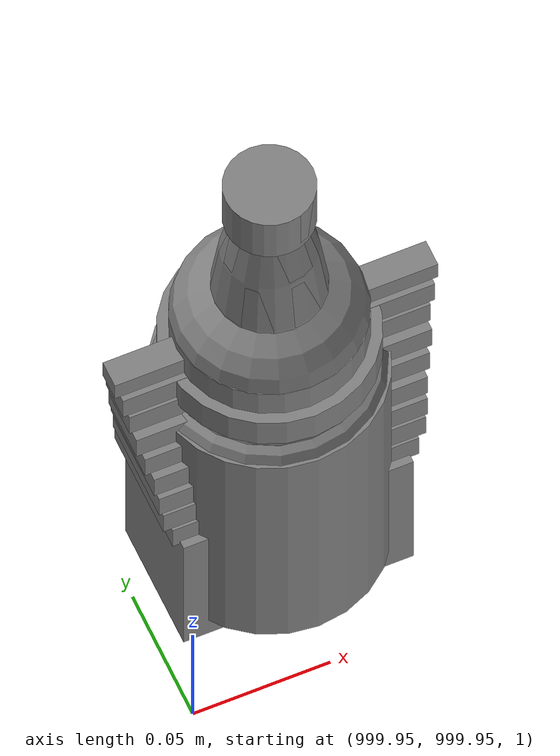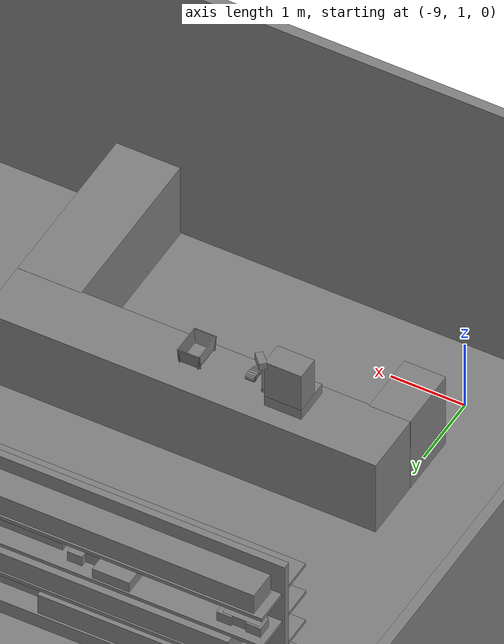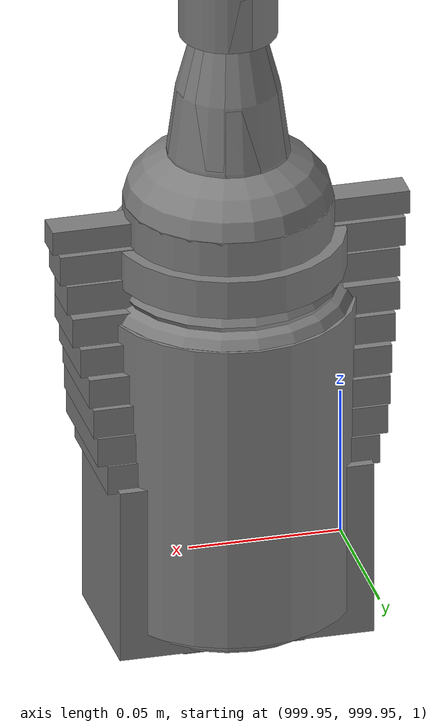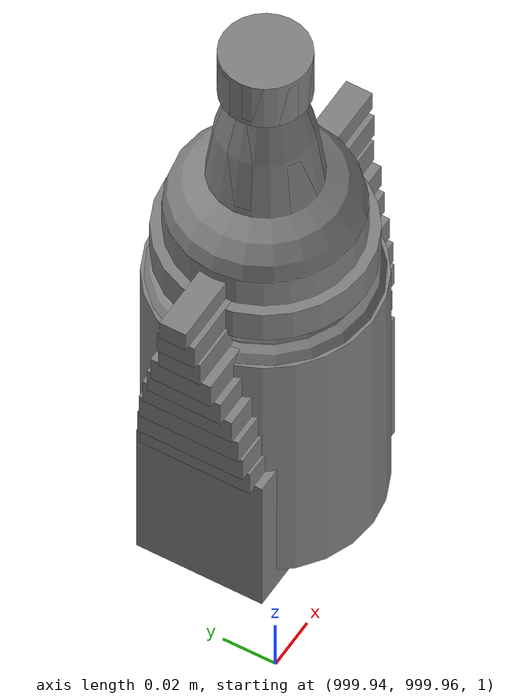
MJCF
<mujoco>
    <option gravity="0.000000000 0.000000000 -9.810000420" timestep="0.0166666" integrator="implicitfast" density="1.225" viscosity="1.8000001e-05" noslip_iterations="10" iterations="100" sdf_iterations="50">
        <flag multiccd="disable"/>
    </option>
    <size memory="1000M"/>
    <compiler coordinate="local"/>
    <worldbody>
        <light cutoff="30" pos="0 1 1" dir="0 -1 -2"/>
        <light cutoff="30" pos="0 -1 1" dir="0 1 -2"/>
        <body pos="0.000000000 0.000000000 0.000000000" euler="0.000000000 0.000000000 0.000000000" name="Interactive Objects_Interactive Objects"/>
        <body pos="1000.000000000 1000.000000000 1.000000000" euler="0.000000000 0.000000000 0.000000000" name="openloong_gripper_2f85_fix_base_usda_bottle_red">
            <geom contype="1" conaffinity="1" density="1000" type="ellipsoid" material="" rgba="0.500000000 0.500000000 0.500000000 1.000000000" solimp="0.899999976 0.949999988 0.001000000" friction="1.000000000 0.005000000 0.000100000" solref="0.020000000 1.000000000" margin="0" condim="3" group="0" pos="0.000000000 0.000000000 0.144284487" quat="1.000000000 0.000000000 0.000000000 0.000000000" size="0.021000000 0.021000000 0.079999998" name="openloong_gripper_2f85_fix_base_usda_geom_F13EC847_5760_4E8A_A5F5_1C7CE25C0754"/>
            <geom contype="1" conaffinity="1" density="1000" type="cylinder" material="" rgba="0.500000000 0.500000000 0.500000000 1.000000000" solimp="0.899999976 0.949999988 0.001000000" friction="1.000000000 0.005000000 0.000100000" solref="0.020000000 1.000000000" margin="0" condim="3" group="0" pos="0.000000000 0.000000000 0.220618963" quat="1.000000000 0.000000000 0.000000000 0.000000000" size="0.016000001 0.010000000 1.000000000" name="openloong_gripper_2f85_fix_base_usda_geom_DA90DCEC_CD66_4DB6_970C_B890051FEF2B"/>
            <geom contype="1" conaffinity="1" density="1000" type="ellipsoid" material="" rgba="0.500000000 0.500000000 0.500000000 1.000000000" solimp="0.899999976 0.949999988 0.001000000" friction="1.000000000 0.005000000 0.000100000" solref="0.020000000 1.000000000" margin="0" condim="3" group="0" pos="0.000000000 0.000000000 0.118945479" quat="1.000000000 0.000000000 0.000000000 0.000000000" size="0.030999999 0.030999999 0.029999999" name="openloong_gripper_2f85_fix_base_usda_geom_CDEB401F_62A9_49D1_A4C8_C05D9224A7CE"/>
            <geom contype="1" conaffinity="1" density="1000" type="box" material="" rgba="0.500000000 0.500000000 0.500000000 1.000000000" solimp="0.899999976 0.949999988 0.001000000" friction="1.000000000 0.005000000 0.000100000" solref="0.020000000 1.000000000" margin="0" condim="3" group="0" pos="0.000000000 0.000000000 0.002189159" quat="1.000000000 0.000000000 0.000000000 0.000000000" size="0.020000000 0.020000000 0.003000000" name="openloong_gripper_2f85_fix_base_usda_geom_D92E5047_D8EE_412B_9E92_5F48484E228A"/>
            <geom contype="1" conaffinity="1" density="1000" type="cylinder" material="" rgba="0.500000000 0.500000000 0.500000000 1.000000000" solimp="0.899999976 0.949999988 0.001000000" friction="1.000000000 0.005000000 0.000100000" solref="0.020000000 1.000000000" margin="0" condim="3" group="0" pos="0.000000000 -0.000366211 0.060884237" quat="1.000000000 0.000000000 0.000000000 0.000000000" size="0.030999999 0.057999998 1.000000000" name="openloong_gripper_2f85_fix_base_usda_geom_349F946B_7A30_4C61_B687_7D94D0866A07"/>
            <freejoint name="openloong_gripper_2f85_fix_base_usda_bottle_red_joint"/>
            <site size="0.005000000 0.005000000 0.005000000" rgba="0.500000000 0.500000000 0.500000000 1.000000000" pos="0.000000000 0.000000000 0.000000000" quat="0.999961913 0.008726535 0.000000000 0.000000000" group="0" type="sphere" name="openloong_gripper_2f85_fix_base_usda_bottle_redsite"/>
        </body>
        <body pos="1000.000000000 1000.000000000 1.000000000" euler="0.000000000 0.000000000 0.000000000" name="openloong_gripper_2f85_fix_base_usda_can">
            <geom contype="1" conaffinity="1" density="1000" type="cylinder" material="" rgba="0.500000000 0.500000000 0.500000000 1.000000000" solimp="0.899999976 0.949999988 0.001000000" friction="1.000000000 0.005000000 0.000100000" solref="0.020000000 1.000000000" margin="0" condim="3" group="0" pos="0.000000000 0.000000000 0.079676986" quat="1.000000000 0.000000000 0.000000000 0.000000000" size="0.034000002 0.071999997 1.000000000" name="openloong_gripper_2f85_fix_base_usda_geom_0142EF4A_4067_486E_9C26_F457C24ABB5E"/>
            <geom contype="1" conaffinity="1" density="1000" type="ellipsoid" material="" rgba="0.500000000 0.500000000 0.500000000 1.000000000" solimp="0.899999976 0.949999988 0.001000000" friction="1.000000000 0.005000000 0.000100000" solref="0.020000000 1.000000000" margin="0" condim="3" group="0" pos="0.000000000 0.000000000 0.151854277" quat="1.000000000 0.000000000 0.000000000 0.000000000" size="0.034000002 0.034000002 0.020000000" name="openloong_gripper_2f85_fix_base_usda_geom_CF1EC406_4F74_4CE5_9F31_947366232800"/>
            <geom contype="1" conaffinity="1" density="1000" type="box" material="" rgba="0.500000000 0.500000000 0.500000000 1.000000000" solimp="0.899999976 0.949999988 0.001000000" friction="1.000000000 0.005000000 0.000100000" solref="0.020000000 1.000000000" margin="0" condim="3" group="0" pos="0.000000000 0.000000000 0.004777670" quat="1.000000000 0.000000000 0.000000000 0.000000000" size="0.020000000 0.020000000 0.005000000" name="openloong_gripper_2f85_fix_base_usda_geom_EDC1FB1F_E036_4804_B224_F75383E132BF"/>
            <freejoint name="openloong_gripper_2f85_fix_base_usda_can_joint"/>
            <site size="0.005000000 0.005000000 0.005000000" rgba="0.500000000 0.500000000 0.500000000 1.000000000" pos="0.000000000 0.000000000 0.000000000" quat="1.000000000 0.000000000 0.000000000 0.000000000" group="0" type="sphere" name="openloong_gripper_2f85_fix_base_usda_cansite"/>
        </body>
        <body pos="-2.039134979 6.194156647 1.830841541" euler="-80.302383423 28.409946442 -34.059154510" mocap="true" name="spotlight2_SpotLight"/>
        <body pos="-1.885096908 6.651095867 1.858255148" euler="-109.823211670 8.798957825 -140.123291016" mocap="true" name="spotlight3_SpotLight"/>
        <body pos="1000.000000000 1000.000000000 1.000000000" euler="0.000000000 0.000000000 0.000000000" name="openloong_gripper_2f85_fix_base_usda_salt">
            <geom contype="1" conaffinity="1" density="1000" type="box" material="" rgba="0.500000000 0.500000000 0.500000000 1.000000000" solimp="0.899999976 0.949999988 0.001000000" friction="1.000000000 0.005000000 0.000100000" solref="0.020000000 1.000000000" margin="0" condim="3" group="0" pos="0.000305176 0.000000000 0.084862232" quat="1.000000000 0.000000000 0.000000000 0.000000000" size="0.048999999 0.018999999 0.005000000" name="openloong_gripper_2f85_fix_base_usda_geom_7FEB3A2B_36B6_4CA5_99E0_AF51899C1AE0"/>
            <geom contype="1" conaffinity="1" density="1000" type="box" material="" rgba="0.500000000 0.500000000 0.500000000 1.000000000" solimp="0.899999976 0.949999988 0.001000000" friction="1.000000000 0.005000000 0.000100000" solref="0.020000000 1.000000000" margin="0" condim="3" group="0" pos="0.000305176 0.000000000 0.104564309" quat="1.000000000 0.000000000 0.000000000 0.000000000" size="0.052000001 0.014000000 0.005000000" name="openloong_gripper_2f85_fix_base_usda_geom_6ED1A141_E709_4256_9C0A_B88373785E13"/>
            <geom contype="1" conaffinity="1" density="1000" type="box" material="" rgba="0.500000000 0.500000000 0.500000000 1.000000000" solimp="0.899999976 0.949999988 0.001000000" friction="1.000000000 0.005000000 0.000100000" solref="0.020000000 1.000000000" margin="0" condim="3" group="0" pos="0.000305176 0.000000000 0.114487171" quat="1.000000000 0.000000000 0.000000000 0.000000000" size="0.054000001 0.011500000 0.005000000" name="openloong_gripper_2f85_fix_base_usda_geom_1AA1828F_DF2B_4D36_99C3_135748A22563"/>
            <geom contype="1" conaffinity="1" density="1000" type="box" material="" rgba="0.500000000 0.500000000 0.500000000 1.000000000" solimp="0.899999976 0.949999988 0.001000000" friction="1.000000000 0.005000000 0.000100000" solref="0.020000000 1.000000000" margin="0" condim="3" group="0" pos="0.000305176 0.000000000 0.075103164" quat="1.000000000 0.000000000 0.000000000 0.000000000" size="0.048000000 0.020000000 0.005000000" name="openloong_gripper_2f85_fix_base_usda_geom_B44C46B1_2EE2_46D5_AC78_1D4F211CEA31"/>
            <geom contype="1" conaffinity="1" density="1000" type="box" material="" rgba="0.500000000 0.500000000 0.500000000 1.000000000" solimp="0.899999976 0.949999988 0.001000000" friction="1.000000000 0.005000000 0.000100000" solref="0.020000000 1.000000000" margin="0" condim="3" group="0" pos="0.000305176 0.000000000 0.134892464" quat="1.000000000 0.000000000 0.000000000 0.000000000" size="0.057000000 0.007000000 0.005000000" name="openloong_gripper_2f85_fix_base_usda_geom_77E5B7ED_D5C9_4F5C_8399_E59EB52A6088"/>
            <geom contype="1" conaffinity="1" density="1000" type="box" material="" rgba="0.500000000 0.500000000 0.500000000 1.000000000" solimp="0.899999976 0.949999988 0.001000000" friction="1.000000000 0.005000000 0.000100000" solref="0.020000000 1.000000000" margin="0" condim="3" group="0" pos="0.000305176 0.000000000 0.094920278" quat="1.000000000 0.000000000 0.000000000 0.000000000" size="0.050000001 0.017000001 0.005000000" name="openloong_gripper_2f85_fix_base_usda_geom_3A88863D_49C0_40EB_B027_6627778639FB"/>
            <geom contype="1" conaffinity="1" density="1000" type="box" material="" rgba="0.500000000 0.500000000 0.500000000 1.000000000" solimp="0.899999976 0.949999988 0.001000000" friction="1.000000000 0.005000000 0.000100000" solref="0.020000000 1.000000000" margin="0" condim="3" group="0" pos="0.000305176 0.000000000 0.065204859" quat="1.000000000 0.000000000 0.000000000 0.000000000" size="0.045000002 0.021000000 0.005000000" name="openloong_gripper_2f85_fix_base_usda_geom_6EB9390A_1454_406A_A8BA_A905F3DF1FDE"/>
            <geom contype="1" conaffinity="1" density="1000" type="box" material="" rgba="0.500000000 0.500000000 0.500000000 1.000000000" solimp="0.899999976 0.949999988 0.001000000" friction="1.000000000 0.005000000 0.000100000" solref="0.020000000 1.000000000" margin="0" condim="3" group="0" pos="0.000305176 0.000000000 0.144135714" quat="1.000000000 0.000000000 0.000000000 0.000000000" size="0.059000000 0.005000000 0.004000000" name="openloong_gripper_2f85_fix_base_usda_geom_DDC4BCCE_A7FF_4155_9526_DAD67AD53F87"/>
            <geom contype="1" conaffinity="1" density="1000" type="box" material="" rgba="0.500000000 0.500000000 0.500000000 1.000000000" solimp="0.899999976 0.949999988 0.001000000" friction="1.000000000 0.005000000 0.000100000" solref="0.020000000 1.000000000" margin="0" condim="3" group="0" pos="0.000000000 0.000000000 0.031593561" quat="1.000000000 0.000000000 0.000000000 0.000000000" size="0.041999999 0.024000000 0.029999999" name="openloong_gripper_2f85_fix_base_usda_geom_B1BE8C89_B300_49A7_A55A_8F693536C416"/>
            <geom contype="1" conaffinity="1" density="1000" type="box" material="" rgba="0.500000000 0.500000000 0.500000000 1.000000000" solimp="0.899999976 0.949999988 0.001000000" friction="1.000000000 0.005000000 0.000100000" solref="0.020000000 1.000000000" margin="0" condim="3" group="0" pos="0.000305176 0.000000000 0.124608755" quat="1.000000000 0.000000000 0.000000000 0.000000000" size="0.055000000 0.008000000 0.005000000" name="openloong_gripper_2f85_fix_base_usda_geom_B098EAAE_2E69_4DE4_A4B9_E8BCEC7C7B4C"/>
            <freejoint name="openloong_gripper_2f85_fix_base_usda_salt_joint"/>
            <site size="0.005000000 0.005000000 0.005000000" rgba="0.500000000 0.500000000 0.500000000 1.000000000" pos="0.000000000 0.000000000 0.000000000" quat="1.000000000 0.000000000 0.000000000 0.000000000" group="0" type="sphere" name="openloong_gripper_2f85_fix_base_usda_saltsite"/>
        </body>
        <body pos="1000.000000000 1000.000000000 1.000000000" euler="0.000000000 0.000000000 0.000000000" name="openloong_gripper_2f85_fix_base_usda_bottle_blue">
            <geom contype="1" conaffinity="1" density="1000" type="ellipsoid" material="" rgba="0.500000000 0.500000000 0.500000000 1.000000000" solimp="0.899999976 0.949999988 0.001000000" friction="1.000000000 0.005000000 0.000100000" solref="0.020000000 1.000000000" margin="0" condim="3" group="0" pos="0.000000000 0.000000000 0.118920922" quat="1.000000000 0.000000000 0.000000000 0.000000000" size="0.030999999 0.030999999 0.029999999" name="openloong_gripper_2f85_fix_base_usda_geom_5DE60869_A87D_4862_95CD_2A31F418B2A9"/>
            <geom contype="1" conaffinity="1" density="1000" type="box" material="" rgba="0.500000000 0.500000000 0.500000000 1.000000000" solimp="0.899999976 0.949999988 0.001000000" friction="1.000000000 0.005000000 0.000100000" solref="0.020000000 1.000000000" margin="0" condim="3" group="0" pos="0.000000000 0.000000000 0.002164602" quat="1.000000000 0.000000000 0.000000000 0.000000000" size="0.020000000 0.020000000 0.003000000" name="openloong_gripper_2f85_fix_base_usda_geom_7CE593C7_75C8_4176_8FA7_D159DB5AD9C1"/>
            <geom contype="1" conaffinity="1" density="1000" type="cylinder" material="" rgba="0.500000000 0.500000000 0.500000000 1.000000000" solimp="0.899999976 0.949999988 0.001000000" friction="1.000000000 0.005000000 0.000100000" solref="0.020000000 1.000000000" margin="0" condim="3" group="0" pos="0.000000000 -0.000366211 0.060859680" quat="1.000000000 0.000000000 0.000000000 0.000000000" size="0.030999999 0.057999998 1.000000000" name="openloong_gripper_2f85_fix_base_usda_geom_4C1E6A7E_FFF8_424A_9C97_9FF796C6EE1E"/>
            <geom contype="1" conaffinity="1" density="1000" type="cylinder" material="" rgba="0.500000000 0.500000000 0.500000000 1.000000000" solimp="0.899999976 0.949999988 0.001000000" friction="1.000000000 0.005000000 0.000100000" solref="0.020000000 1.000000000" margin="0" condim="3" group="0" pos="0.000000000 0.000000000 0.220594406" quat="1.000000000 0.000000000 0.000000000 0.000000000" size="0.016000001 0.010000000 1.000000000" name="openloong_gripper_2f85_fix_base_usda_geom_A933375D_8322_4AD8_88AE_1E63E7F6BF5C"/>
            <geom contype="1" conaffinity="1" density="1000" type="ellipsoid" material="" rgba="0.500000000 0.500000000 0.500000000 1.000000000" solimp="0.899999976 0.949999988 0.001000000" friction="1.000000000 0.005000000 0.000100000" solref="0.020000000 1.000000000" margin="0" condim="3" group="0" pos="0.000000000 0.000000000 0.144259930" quat="1.000000000 0.000000000 0.000000000 0.000000000" size="0.021000000 0.021000000 0.079999998" name="openloong_gripper_2f85_fix_base_usda_geom_A0F2E8B5_8DBD_44C3_B0AF_649A34189A6D"/>
            <freejoint name="openloong_gripper_2f85_fix_base_usda_bottle_blue_joint"/>
            <site size="0.005000000 0.005000000 0.005000000" rgba="0.500000000 0.500000000 0.500000000 1.000000000" pos="0.000000000 0.000000000 0.000000000" quat="0.999961913 0.008726535 0.000000000 0.000000000" group="0" type="sphere" name="openloong_gripper_2f85_fix_base_usda_bottle_bluesite"/>
        </body>
        <body pos="-2.196951628 6.664298534 1.821402550" euler="-105.481987000 -31.468278885 -36.062454224" mocap="true" name="spotlight4_SpotLight"/>
        <body pos="1000.000000000 1000.000000000 1.000000000" euler="0.000000000 0.000000000 0.000000000" name="openloong_gripper_2f85_fix_base_usda_jar_01">
            <geom contype="1" conaffinity="1" density="1000" type="box" material="" rgba="0.500000000 0.500000000 0.500000000 1.000000000" solimp="0.899999976 0.949999988 0.001000000" friction="1.000000000 0.005000000 0.000100000" solref="0.020000000 1.000000000" margin="0" condim="3" group="0" pos="0.000000000 0.000000000 0.006158113" quat="1.000000000 0.000000000 0.000000000 0.000000000" size="0.020000000 0.020000000 0.005000000" name="openloong_gripper_2f85_fix_base_usda_geom_90E8E3DC_76ED_4BA7_BE78_DBA5422B516F"/>
            <geom contype="1" conaffinity="1" density="1000" type="cylinder" material="" rgba="0.500000000 0.500000000 0.500000000 1.000000000" solimp="0.899999976 0.949999988 0.001000000" friction="1.000000000 0.005000000 0.000100000" solref="0.020000000 1.000000000" margin="0" condim="3" group="0" pos="0.000000000 0.000000000 0.062744498" quat="1.000000000 0.000000000 0.000000000 0.000000000" size="0.041000001 0.052999999 1.000000000" name="openloong_gripper_2f85_fix_base_usda_geom_770A7DDC_4B9A_47E7_8E94_85B5A700C4D8"/>
            <geom contype="1" conaffinity="1" density="1000" type="ellipsoid" material="" rgba="0.500000000 0.500000000 0.500000000 1.000000000" solimp="0.899999976 0.949999988 0.001000000" friction="1.000000000 0.005000000 0.000100000" solref="0.020000000 1.000000000" margin="0" condim="3" group="0" pos="0.000000000 0.000000000 0.122252703" quat="1.000000000 0.000000000 0.000000000 0.000000000" size="0.035999998 0.035999998 0.010000000" name="openloong_gripper_2f85_fix_base_usda_geom_5019EA22_875B_483C_A881_2E8F23071039"/>
            <geom contype="1" conaffinity="1" density="1000" type="cylinder" material="" rgba="0.500000000 0.500000000 0.500000000 1.000000000" solimp="0.899999976 0.949999988 0.001000000" friction="1.000000000 0.005000000 0.000100000" solref="0.020000000 1.000000000" margin="0" condim="3" group="0" pos="0.000000000 0.000000000 0.015747190" quat="1.000000000 0.000000000 0.000000000 0.000000000" size="0.035000000 0.010000000 1.000000000" name="openloong_gripper_2f85_fix_base_usda_geom_2900E8B5_2D18_41A0_A975_08290F2FE136"/>
            <geom contype="1" conaffinity="1" density="1000" type="ellipsoid" material="" rgba="0.500000000 0.500000000 0.500000000 1.000000000" solimp="0.899999976 0.949999988 0.001000000" friction="1.000000000 0.005000000 0.000100000" solref="0.020000000 1.000000000" margin="0" condim="3" group="0" pos="0.000000000 0.000000000 0.115815401" quat="1.000000000 0.000000000 0.000000000 0.000000000" size="0.039999999 0.039999999 0.010000000" name="openloong_gripper_2f85_fix_base_usda_geom_32798564_2CE5_4C03_BE22_DFFE573E878B"/>
            <geom contype="1" conaffinity="1" density="1000" type="cylinder" material="" rgba="0.500000000 0.500000000 0.500000000 1.000000000" solimp="0.899999976 0.949999988 0.001000000" friction="1.000000000 0.005000000 0.000100000" solref="0.020000000 1.000000000" margin="0" condim="3" group="0" pos="0.000000000 0.000000000 0.133183479" quat="1.000000000 0.000000000 0.000000000 0.000000000" size="0.037999999 0.006500000 1.000000000" name="openloong_gripper_2f85_fix_base_usda_geom_B69F07F4_9302_41CA_BF57_DF665704433E"/>
            <freejoint name="openloong_gripper_2f85_fix_base_usda_jar_01_joint"/>
            <site size="0.005000000 0.005000000 0.005000000" rgba="0.500000000 0.500000000 0.500000000 1.000000000" pos="0.000000000 0.000000000 0.000000000" quat="1.000000000 0.000000000 0.000000000 0.000000000" group="0" type="sphere" name="openloong_gripper_2f85_fix_base_usda_jar_01site"/>
        </body>
        <body pos="0.000000000 0.000000000 0.000000000" euler="0.000000000 0.000000000 0.000000000" name=" Static Objects_ Static Objects">
            <geom contype="1" conaffinity="1" density="1000" type="box" material="" rgba="0.500000000 0.500000000 0.500000000 1.000000000" solimp="0.899999976 0.949999988 0.001000000" friction="1.000000000 0.005000000 0.000100000" solref="0.020000000 1.000000000" margin="0" condim="3" group="0" pos="-3.101639986 6.150595188 1.018643856" quat="1.000000000 0.000000000 0.000000000 0.000000000" size="0.050000001 0.579999983 1.019999981" name=" Static Objects_geom_A1DBA70C_D365_4428_9CE2_00FE5A3AAF36"/>
            <geom contype="1" conaffinity="1" density="1000" type="box" material="" rgba="0.500000000 0.500000000 0.500000000 1.000000000" solimp="0.899999976 0.949999988 0.001000000" friction="1.000000000 0.005000000 0.000100000" solref="0.020000000 1.000000000" margin="0" condim="3" group="0" pos="-2.825197220 6.153595448 1.115278244" quat="0.707107067 0.000000000 0.000000000 0.707106471" size="0.550000012 0.239999995 0.025000000" name=" Static Objects_geom_94009957_DB50_44A9_A7EF_63B3B56D0320"/>
            <geom contype="1" conaffinity="1" density="1000" type="box" material="" rgba="0.500000000 0.500000000 0.500000000 1.000000000" solimp="0.899999976 0.949999988 0.001000000" friction="1.000000000 0.005000000 0.000100000" solref="0.020000000 1.000000000" margin="0" condim="3" group="0" pos="-2.825197220 6.153595448 0.097434282" quat="0.707107067 0.000000000 0.000000000 0.707106471" size="0.550000012 0.239999995 0.098999999" name=" Static Objects_geom_4CBBE403_A516_4AE2_9C46_41EA51710AC2"/>
            <geom contype="1" conaffinity="1" density="1000" type="box" material="" rgba="0.500000000 0.500000000 0.500000000 1.000000000" solimp="0.899999976 0.949999988 0.001000000" friction="1.000000000 0.005000000 0.000100000" solref="0.020000000 1.000000000" margin="0" condim="3" group="0" pos="-6.293097973 6.153595448 1.114443064" quat="0.707107067 0.000000000 0.000000000 0.707106471" size="0.529999971 3.134999990 0.025000000" name=" Static Objects_geom_FEA1C2A5_6E9D_4A2B_8367_652CC9BABF82"/>
            <geom contype="1" conaffinity="1" density="1000" type="box" material="" rgba="0.500000000 0.500000000 0.500000000 1.000000000" solimp="0.899999976 0.949999988 0.001000000" friction="1.000000000 0.005000000 0.000100000" solref="0.020000000 1.000000000" margin="0" condim="3" group="0" pos="-6.286010742 6.153595448 0.096129179" quat="0.707107067 0.000000000 0.000000000 0.707106471" size="0.529999971 3.134999990 0.098999999" name=" Static Objects_geom_A6DEA62E_226A_4E52_B773_09B94AC1DE49"/>
            <geom contype="1" conaffinity="1" density="1000" type="box" material="" rgba="0.500000000 0.500000000 0.500000000 1.000000000" solimp="0.899999976 0.949999988 0.001000000" friction="1.000000000 0.005000000 0.000100000" solref="0.020000000 1.000000000" margin="0" condim="3" group="0" pos="-2.825197220 6.153595448 1.563861728" quat="0.707107067 0.000000000 0.000000000 0.707106471" size="0.550000012 0.239999995 0.025000000" name=" Static Objects_geom_318AA18E_EBA6_41A0_BC2A_056984C28406"/>
            <geom contype="1" conaffinity="1" density="1000" type="box" material="" rgba="0.500000000 0.500000000 0.500000000 1.000000000" solimp="0.899999976 0.949999988 0.001000000" friction="1.000000000 0.005000000 0.000100000" solref="0.020000000 1.000000000" margin="0" condim="3" group="0" pos="-6.311686516 6.153595448 1.018643856" quat="0.707107067 0.000000000 0.000000000 0.707106471" size="0.050000001 3.150000095 1.019999981" name=" Static Objects_geom_5D7A1E61_CC68_4F33_AE62_ED9609D79AC4"/>
            <geom contype="1" conaffinity="1" density="1000" type="box" material="" rgba="0.500000000 0.500000000 0.500000000 1.000000000" solimp="0.899999976 0.949999988 0.001000000" friction="1.000000000 0.005000000 0.000100000" solref="0.020000000 1.000000000" margin="0" condim="3" group="0" pos="-2.825197220 6.153595448 0.629031777" quat="0.707107067 0.000000000 0.000000000 0.707106471" size="0.550000012 0.239999995 0.025000000" name=" Static Objects_geom_82A71097_824F_4A82_B998_76128635BFB6"/>
            <geom contype="1" conaffinity="1" density="1000" type="box" material="" rgba="0.500000000 0.500000000 0.500000000 1.000000000" solimp="0.899999976 0.949999988 0.001000000" friction="1.000000000 0.005000000 0.000100000" solref="0.020000000 1.000000000" margin="0" condim="3" group="0" pos="-6.286010742 6.153595448 1.563861728" quat="0.707107067 0.000000000 0.000000000 0.707106471" size="0.529999971 3.134999990 0.025000000" name=" Static Objects_geom_2C004ADA_2FC2_48B4_971E_604E5F084948"/>
            <geom contype="1" conaffinity="1" density="1000" type="box" material="" rgba="0.500000000 0.500000000 0.500000000 1.000000000" solimp="0.899999976 0.949999988 0.001000000" friction="1.000000000 0.005000000 0.000100000" solref="0.020000000 1.000000000" margin="0" condim="3" group="0" pos="-6.286010742 6.153595448 0.629031777" quat="0.707107067 0.000000000 0.000000000 0.707106471" size="0.529999971 3.134999990 0.025000000" name=" Static Objects_geom_7991DD75_6946_4AB0_BF0C_540689E90A6A"/>
            <geom contype="1" conaffinity="1" density="1000" type="box" material="" rgba="0.500000000 0.500000000 0.500000000 1.000000000" solimp="0.899999976 0.949999988 0.001000000" friction="1.000000000 0.005000000 0.000100000" solref="0.020000000 1.000000000" margin="0" condim="3" group="0" pos="-7.719123363 2.867671013 1.173410416" quat="1.000000000 0.000000000 0.000000000 0.000000000" size="0.250000000 0.250000000 0.079999998" name=" Static Objects_geom_C25416CA_BA40_49E4_9CF9_AD2B54196084"/>
            <geom contype="1" conaffinity="1" density="1000" type="box" material="" rgba="0.500000000 0.500000000 0.500000000 1.000000000" solimp="0.899999976 0.949999988 0.001000000" friction="1.000000000 0.005000000 0.000100000" solref="0.020000000 1.000000000" margin="0" condim="3" group="0" pos="-7.408766270 3.088089943 1.776644945" quat="0.928051054 0.000000000 0.000000000 0.372453064" size="0.050000001 0.100000001 0.050000001" name=" Static Objects_geom_232A3975_7D46_4E1F_83CC_39FFFA8F2EEB"/>
            <geom contype="1" conaffinity="1" density="1000" type="box" material="" rgba="0.500000000 0.500000000 0.500000000 1.000000000" solimp="0.899999976 0.949999988 0.001000000" friction="1.000000000 0.005000000 0.000100000" solref="0.020000000 1.000000000" margin="0" condim="3" group="0" pos="-7.719123363 2.958004713 1.530241251" quat="1.000000000 0.000000000 0.000000000 0.000000000" size="0.250000000 0.159999996 0.280000001" name=" Static Objects_geom_B21008C8_A46D_418F_8E73_0664E820C02A"/>
            <geom contype="1" conaffinity="1" density="1000" type="cylinder" material="" rgba="0.500000000 0.500000000 0.500000000 1.000000000" solimp="0.899999976 0.949999988 0.001000000" friction="1.000000000 0.005000000 0.000100000" solref="0.020000000 1.000000000" margin="0" condim="3" group="0" pos="-7.427312374 3.069516420 1.502544641" quat="0.928051054 0.000000000 0.000000000 0.372453064" size="0.015000000 0.230000004 0.100000001" name=" Static Objects_geom_064EEC73_293D_4013_9200_24AC619CAB80"/>
            <geom contype="1" conaffinity="1" density="1000" type="box" material="" rgba="0.500000000 0.500000000 0.500000000 1.000000000" solimp="0.899999976 0.949999988 0.001000000" friction="1.000000000 0.005000000 0.000100000" solref="0.020000000 1.000000000" margin="0" condim="3" group="0" pos="-7.437745571 3.067511320 1.289965630" quat="1.000000000 0.000000000 0.000000000 0.000000000" size="0.029999999 0.020000000 0.020000000" name=" Static Objects_geom_2861354C_59AE_4D7D_B975_F863460666CC"/>
            <geom contype="1" conaffinity="1" density="1000" type="box" material="" rgba="0.500000000 0.500000000 0.500000000 1.000000000" solimp="0.899999976 0.949999988 0.001000000" friction="1.000000000 0.005000000 0.000100000" solref="0.020000000 1.000000000" margin="0" condim="3" group="0" pos="-9.058088303 6.434794426 1.209077358" quat="1.000000000 0.000000000 0.000000000 0.000000000" size="0.250000000 0.100000001 0.070000000" name=" Static Objects_geom_7E67B858_EE2A_4CBB_BB07_D2CD137A5646"/>
            <geom contype="1" conaffinity="1" density="1000" type="box" material="" rgba="0.500000000 0.500000000 0.500000000 1.000000000" solimp="0.899999976 0.949999988 0.001000000" friction="1.000000000 0.005000000 0.000100000" solref="0.020000000 1.000000000" margin="0" condim="3" group="0" pos="-7.886891365 6.459744930 0.352518857" quat="1.000000000 0.000000000 0.000000000 0.000000000" size="1.500000000 0.200000003 0.150000006" name=" Static Objects_geom_8036EC19_141D_4E7F_924F_FAD3581B3351"/>
            <geom contype="1" conaffinity="1" density="1000" type="box" material="" rgba="0.500000000 0.500000000 0.500000000 1.000000000" solimp="0.899999976 0.949999988 0.001000000" friction="1.000000000 0.005000000 0.000100000" solref="0.020000000 1.000000000" margin="0" condim="3" group="0" pos="-9.237723351 6.464855671 1.209077358" quat="1.000000000 0.000000000 0.000000000 0.000000000" size="0.100000001 0.100000001 0.070000000" name=" Static Objects_geom_DAC95187_25EE_46E0_B662_451B09F3790E"/>
            <geom contype="1" conaffinity="1" density="1000" type="box" material="" rgba="0.500000000 0.500000000 0.500000000 1.000000000" solimp="0.899999976 0.949999988 0.001000000" friction="1.000000000 0.005000000 0.000100000" solref="0.020000000 1.000000000" margin="0" condim="3" group="0" pos="-6.924745083 6.362090111 1.214329123" quat="1.000000000 0.000000000 0.000000000 0.000000000" size="0.200000003 0.100000001 0.075000003" name=" Static Objects_geom_7481492A_B0E0_449D_839F_C08769E4DEB3"/>
            <geom contype="1" conaffinity="1" density="1000" type="box" material="" rgba="0.500000000 0.500000000 0.500000000 1.000000000" solimp="0.899999976 0.949999988 0.001000000" friction="1.000000000 0.005000000 0.000100000" solref="0.020000000 1.000000000" margin="0" condim="3" group="0" pos="-4.407354832 6.459744930 1.292199373" quat="1.000000000 0.000000000 0.000000000 0.000000000" size="1.240000010 0.200000003 0.150000006" name=" Static Objects_geom_F437714B_5DB0_4F9A_96DF_4068C6968F76"/>
            <geom contype="1" conaffinity="1" density="1000" type="box" material="" rgba="0.500000000 0.500000000 0.500000000 1.000000000" solimp="0.899999976 0.949999988 0.001000000" friction="1.000000000 0.005000000 0.000100000" solref="0.020000000 1.000000000" margin="0" condim="3" group="0" pos="-5.611940861 6.318420410 0.350975692" quat="1.000000000 0.000000000 0.000000000 0.000000000" size="0.699999988 0.100000001 0.150000006" name=" Static Objects_geom_48E4CB2B_A3A6_4289_A8CD_CAEB487E33F6"/>
            <geom contype="1" conaffinity="1" density="1000" type="box" material="" rgba="0.500000000 0.500000000 0.500000000 1.000000000" solimp="0.899999976 0.949999988 0.001000000" friction="1.000000000 0.005000000 0.000100000" solref="0.020000000 1.000000000" margin="0" condim="3" group="0" pos="-6.300771236 6.459744930 1.744376063" quat="1.000000000 0.000000000 0.000000000 0.000000000" size="3.000000000 0.200000003 0.150000006" name=" Static Objects_geom_45697DAD_3F4C_492A_823E_3389C866D349"/>
            <geom contype="1" conaffinity="1" density="1000" type="box" material="" rgba="0.500000000 0.500000000 0.500000000 1.000000000" solimp="0.899999976 0.949999988 0.001000000" friction="1.000000000 0.005000000 0.000100000" solref="0.020000000 1.000000000" margin="0" condim="3" group="0" pos="-6.751636982 6.459744930 0.800981164" quat="1.000000000 0.000000000 0.000000000 0.000000000" size="2.200000048 0.200000003 0.150000006" name=" Static Objects_geom_A1B64F44_706F_4120_8CE7_C638D564EF24"/>
            <geom contype="1" conaffinity="1" density="1000" type="box" material="" rgba="0.500000000 0.500000000 0.500000000 1.000000000" solimp="0.899999976 0.949999988 0.001000000" friction="1.000000000 0.005000000 0.000100000" solref="0.020000000 1.000000000" margin="0" condim="3" group="0" pos="-8.844120979 6.464855671 1.209077358" quat="1.000000000 0.000000000 0.000000000 0.000000000" size="0.100000001 0.100000001 0.070000000" name=" Static Objects_geom_B93B429F_C8B6_4527_A2FD_C39687D6FDE9"/>
            <geom contype="1" conaffinity="1" density="1000" type="box" material="" rgba="0.500000000 0.500000000 0.500000000 1.000000000" solimp="0.899999976 0.949999988 0.001000000" friction="1.000000000 0.005000000 0.000100000" solref="0.020000000 1.000000000" margin="0" condim="3" group="0" pos="-6.098561764 6.327973843 1.292199373" quat="1.000000000 0.000000000 0.000000000 0.000000000" size="0.500000000 0.100000001 0.150000006" name=" Static Objects_geom_B2B0DECF_19A1_4420_AB86_CBEEFCF7CAB7"/>
            <geom contype="1" conaffinity="1" density="1000" type="box" material="" rgba="0.500000000 0.500000000 0.500000000 1.000000000" solimp="0.899999976 0.949999988 0.001000000" friction="1.000000000 0.005000000 0.000100000" solref="0.020000000 1.000000000" margin="0" condim="3" group="0" pos="-6.824534416 6.447464466 1.212718010" quat="1.000000000 0.000000000 0.000000000 0.000000000" size="0.100000001 0.100000001 0.075000003" name=" Static Objects_geom_F9900730_27CC_4276_8F1D_7113A8C1E64E"/>
            <geom contype="1" conaffinity="1" density="1000" type="box" material="" rgba="0.500000000 0.500000000 0.500000000 1.000000000" solimp="0.899999976 0.949999988 0.001000000" friction="1.000000000 0.005000000 0.000100000" solref="0.020000000 1.000000000" margin="0" condim="3" group="0" pos="-3.907610416 6.318625927 0.800981164" quat="1.000000000 0.000000000 0.000000000 0.000000000" size="0.500000000 0.100000001 0.150000006" name=" Static Objects_geom_93238858_CA56_489C_AED5_0EDA9FA0AC85"/>
            <geom contype="1" conaffinity="1" density="1000" type="box" material="" rgba="0.500000000 0.500000000 0.500000000 1.000000000" solimp="0.899999976 0.949999988 0.001000000" friction="1.000000000 0.005000000 0.000100000" solref="0.020000000 1.000000000" margin="0" condim="3" group="0" pos="-7.373087406 6.458900928 1.214329123" quat="1.000000000 0.000000000 0.000000000 0.000000000" size="0.250000000 0.200000003 0.075000003" name=" Static Objects_geom_48E90C4E_0CA4_4BBF_91E6_0D65F992EB0F"/>
            <geom contype="1" conaffinity="1" density="1000" type="box" material="" rgba="0.500000000 0.500000000 0.500000000 1.000000000" solimp="0.899999976 0.949999988 0.001000000" friction="1.000000000 0.005000000 0.000100000" solref="0.020000000 1.000000000" margin="0" condim="3" group="0" pos="-4.035642624 6.459744930 0.352518857" quat="1.000000000 0.000000000 0.000000000 0.000000000" size="0.800000012 0.200000003 0.150000006" name=" Static Objects_geom_4503FE8E_39F2_4883_BA17_D90AFF45B4B6"/>
            <geom contype="1" conaffinity="1" density="1000" type="box" material="" rgba="0.500000000 0.500000000 0.500000000 1.000000000" solimp="0.899999976 0.949999988 0.001000000" friction="1.000000000 0.005000000 0.000100000" solref="0.020000000 1.000000000" margin="0" condim="3" group="0" pos="-6.460197449 2.937205315 0.548931718" quat="1.000000000 0.000000000 0.000000000 0.000000000" size="2.650000095 0.430000007 0.550000012" name=" Static Objects_geom_06E997F3_5DE3_4F4C_8EB9_BEF3228F7CAF"/>
            <geom contype="1" conaffinity="1" density="1000" type="box" material="" rgba="0.500000000 0.500000000 0.500000000 1.000000000" solimp="0.899999976 0.949999988 0.001000000" friction="1.000000000 0.005000000 0.000100000" solref="0.020000000 1.000000000" margin="0" condim="3" group="0" pos="-4.240264893 1.327049494 0.549888909" quat="1.000000000 0.000000000 0.000000000 0.000000000" size="0.430000007 1.200000048 0.550000012" name=" Static Objects_geom_ADB4B7AF_4EC4_4D12_BEBE_2D53772C83FB"/>
            <geom contype="1" conaffinity="1" density="1000" type="box" material="" rgba="0.500000000 0.500000000 0.500000000 1.000000000" solimp="0.899999976 0.949999988 0.001000000" friction="1.000000000 0.005000000 0.000100000" solref="0.020000000 1.000000000" margin="0" condim="3" group="0" pos="-8.830721855 2.096410990 0.549305558" quat="1.000000000 0.000000000 0.000000000 0.000000000" size="0.280000001 0.430000007 0.550000012" name=" Static Objects_geom_6025616C_25BF_4444_B5D8_C378F9CC6179"/>
            <geom contype="1" conaffinity="1" density="1000" type="plane" material="" rgba="0.500000000 0.500000000 0.500000000 1.000000000" solimp="0.899999976 0.949999988 0.001000000" friction="1.000000000 0.005000000 0.000100000" solref="0.020000000 1.000000000" margin="0" condim="3" group="0" pos="-6.000000000 10.399999619 0.000000000" quat="1.000000000 0.000000000 0.000000000 0.000000000" size="6.050000191 10.800000191 0.010000000" name=" Static Objects_geom_E0C93D7A_B699_4B1D_9E3F_A9F7481774F0"/>
            <geom contype="1" conaffinity="1" density="1000" type="box" material="" rgba="0.500000000 0.500000000 0.500000000 1.000000000" solimp="0.899999976 0.949999988 0.001000000" friction="1.000000000 0.005000000 0.000100000" solref="0.020000000 1.000000000" margin="0" condim="3" group="0" pos="-6.000000000 0.035000000 2.000000000" quat="1.000000000 0.000000000 0.000000000 0.000000000" size="6.079999924 0.070000000 2.000000000" name=" Static Objects_geom_DCE3617E_DB75_4267_80D4_4170BF01A8DF"/>
            <geom contype="1" conaffinity="1" density="1000" type="box" material="" rgba="0.500000000 0.500000000 0.500000000 1.000000000" solimp="0.899999976 0.949999988 0.001000000" friction="1.000000000 0.005000000 0.000100000" solref="0.020000000 1.000000000" margin="0" condim="3" group="0" pos="-6.000000000 20.159999847 2.000000000" quat="1.000000000 0.000000000 0.000000000 0.000000000" size="6.079999924 0.070000000 2.000000000" name=" Static Objects_geom_785C5B9D_7124_4C7C_B2CB_26A3FF1B6EED"/>
            <geom contype="1" conaffinity="1" density="1000" type="box" material="" rgba="0.500000000 0.500000000 0.500000000 1.000000000" solimp="0.899999976 0.949999988 0.001000000" friction="1.000000000 0.005000000 0.000100000" solref="0.020000000 1.000000000" margin="0" condim="3" group="0" pos="0.000000000 10.000000000 2.000000000" quat="1.000000000 0.000000000 0.000000000 0.000000000" size="0.070000000 10.500000000 2.000000000" name=" Static Objects_geom_CD49BDC3_CA0F_49BE_A0E6_51C05C19FA6A"/>
            <geom contype="1" conaffinity="1" density="1000" type="box" material="" rgba="0.500000000 0.500000000 0.500000000 1.000000000" solimp="0.899999976 0.949999988 0.001000000" friction="1.000000000 0.005000000 0.000100000" solref="0.020000000 1.000000000" margin="0" condim="3" group="0" pos="-12.050000191 10.000000000 2.000000000" quat="1.000000000 0.000000000 0.000000000 0.000000000" size="0.070000000 10.500000000 2.000000000" name=" Static Objects_geom_06F839C7_1741_45F2_AFB0_13906EB9A6DE"/>
        </body>
        <body pos="-3.510578632 3.403555870 -0.000000100" euler="0.000000000 0.000000000 40.200675964" name="openloong_gripper_2f85_fix_base_usda_PZ">
            <geom contype="1" conaffinity="1" density="1000" type="box" material="" rgba="0.500000000 0.500000000 0.500000000 1.000000000" solimp="0.899999976 0.949999988 0.001000000" friction="1.000000000 0.005000000 0.000100000" solref="0.020000000 1.000000000" margin="0" condim="3" group="0" pos="-0.047453165 0.056484699 0.373715430" quat="0.934750080 0.077914521 0.028795123 0.345459938" size="0.180000007 0.010000000 0.379999995" name="openloong_gripper_2f85_fix_base_usda_geom_299D0FFE_CB26_4255_ABC6_C10A3E09D9DD"/>
            <geom contype="1" conaffinity="1" density="1000" type="box" material="" rgba="0.500000000 0.500000000 0.500000000 1.000000000" solimp="0.899999976 0.949999988 0.001000000" friction="1.000000000 0.005000000 0.000100000" solref="0.020000000 1.000000000" margin="0" condim="3" group="0" pos="0.047452450 -0.054376602 0.374072611" quat="0.934387863 -0.082143910 -0.030358355 0.345326364" size="0.180000007 0.010000000 0.379999995" name="openloong_gripper_2f85_fix_base_usda_geom_252FC271_4AC6_48CA_AE19_732924965F9A"/>
            <freejoint name="openloong_gripper_2f85_fix_base_usda_PZ"/>
        </body>
        <body pos="-6.332345009 2.779978037 1.034067392" euler="0.000000000 0.000000000 0.000000000" name="openloong_gripper_2f85_fix_base_usda_basket">
            <geom contype="1" conaffinity="1" density="100000" type="box" material="" rgba="0.500000000 0.500000000 0.500000000 1.000000000" solimp="0.899999976 0.949999988 0.001000000" friction="1.000000000 0.899999976 0.000100000" solref="0.020000000 1.000000000" margin="0" condim="3" group="0" pos="-0.172339439 0.000000000 0.168361664" quat="0.706172407 -0.036353018 -0.036353093 0.706170976" size="0.200000003 0.006000000 0.108000003" name="openloong_gripper_2f85_fix_base_usda_geom_97FFAF3F_A805_4511_A883_2E94D1A8482A"/>
            <geom contype="1" conaffinity="1" density="100000" type="box" material="" rgba="0.500000000 0.500000000 0.500000000 1.000000000" solimp="0.899999976 0.949999988 0.001000000" friction="1.000000000 0.899999976 0.000100000" solref="0.020000000 1.000000000" margin="0" condim="3" group="0" pos="-0.039724827 -0.188568115 0.167089701" quat="0.997537494 0.070135131 0.000000000 0.000000000" size="0.150000006 0.006000000 0.108000003" name="openloong_gripper_2f85_fix_base_usda_geom_033B4E4C_4A51_4102_B1D3_66C3D67A97B0"/>
            <geom contype="1" conaffinity="1" density="100000" type="box" material="" rgba="0.500000000 0.500000000 0.500000000 1.000000000" solimp="0.899999976 0.949999988 0.001000000" friction="1.000000000 0.899999976 0.000100000" solref="0.020000000 1.000000000" margin="0" condim="3" group="0" pos="-0.039724827 0.188377380 0.167089701" quat="0.997489929 -0.070808925 0.000000000 0.000000000" size="0.150000006 0.006000000 0.108000003" name="openloong_gripper_2f85_fix_base_usda_geom_F0C3336C_838D_4498_B676_A2FA772ABF52"/>
            <geom contype="1" conaffinity="1" density="100000" type="box" material="" rgba="0.500000000 0.500000000 0.500000000 1.000000000" solimp="0.899999976 0.949999988 0.001000000" friction="1.000000000 0.899999976 0.000100000" solref="0.020000000 1.000000000" margin="0" condim="3" group="0" pos="-0.039724827 0.000000000 0.068126202" quat="1.000000000 0.000000000 0.000000000 0.000000000" size="0.129999995 0.174999997 0.006000000" name="openloong_gripper_2f85_fix_base_usda_geom_3E8F853F_1C1D_41FA_90C7_0C6A2E233AB2"/>
            <geom contype="1" conaffinity="1" density="100000" type="box" material="" rgba="0.500000000 0.500000000 0.500000000 1.000000000" solimp="0.899999976 0.949999988 0.001000000" friction="1.000000000 0.899999976 0.000100000" solref="0.020000000 1.000000000" margin="0" condim="3" group="0" pos="0.094372749 0.000000000 0.168361664" quat="0.706172049 0.036353335 0.036353379 0.706171215" size="0.200000003 0.006000000 0.108000003" name="openloong_gripper_2f85_fix_base_usda_geom_E053D0E1_3D9D_416C_A3B1_66F14D5AD8D6"/>
            <freejoint name="openloong_gripper_2f85_fix_base_usda_basket_joint"/>
            <site size="0.005000000 0.005000000 0.005000000" rgba="0.500000000 0.500000000 0.500000000 1.000000000" pos="0.000000000 0.000000000 0.000000000" quat="1.000000000 0.000000000 0.000000000 0.000000000" group="0" type="sphere" name="openloong_gripper_2f85_fix_base_usda_basketsite"/>
        </body>
        <body pos="-2.436573029 6.404376507 0.137849092" euler="0.000000000 0.000000000 0.000000000" name="openloong_gripper_2f85_fix_base_usda_shoppingtrolley_01">
            <geom contype="1" conaffinity="1" density="1000" type="box" material="" rgba="0.500000000 0.500000000 0.500000000 1.000000000" solimp="0.899999976 0.949999988 0.001000000" friction="1.000000000 0.005000000 0.000100000" solref="0.020000000 1.000000000" margin="0" condim="3" group="0" pos="-0.169898406 -0.178061336 0.864131629" quat="0.916343808 -0.400392294 -0.000000045 0.000000030" size="0.017999999 0.022499999 0.089999996" name="openloong_gripper_2f85_fix_base_usda_geom_1C254FA7_4671_487D_B013_2D3479D4B435"/>
            <geom contype="1" conaffinity="1" density="1000" type="box" material="" rgba="0.500000000 0.500000000 0.500000000 1.000000000" solimp="0.899999976 0.949999988 0.001000000" friction="1.000000000 0.005000000 0.000100000" solref="0.020000000 1.000000000" margin="0" condim="3" group="0" pos="-0.107458733 0.238907143 0.911498845" quat="0.634576976 0.622505128 -0.330067992 -0.317575932" size="0.017999999 0.022499999 0.035999998" name="openloong_gripper_2f85_fix_base_usda_geom_98E04339_E2A1_4076_8450_630B93EE239F"/>
            <geom contype="1" conaffinity="1" density="1000" type="box" material="" rgba="0.500000000 0.500000000 0.500000000 1.000000000" solimp="0.899999976 0.949999988 0.001000000" friction="1.000000000 0.005000000 0.000100000" solref="0.020000000 1.000000000" margin="0" condim="3" group="0" pos="-0.005004787 0.248085022 0.912686050" quat="1.000000000 0.000000000 0.000000000 0.000000000" size="0.107999995 0.022499999 0.022499999" name="openloong_gripper_2f85_fix_base_usda_geom_CDC167B9_8FB8_4EE2_B5EC_5E370899C14B"/>
            <geom contype="1" conaffinity="1" density="1000" type="box" material="" rgba="0.500000000 0.500000000 0.500000000 1.000000000" solimp="0.899999976 0.949999988 0.001000000" friction="1.000000000 0.005000000 0.000100000" solref="0.020000000 1.000000000" margin="0" condim="3" group="0" pos="0.131482959 -0.182533979 0.598989725" quat="0.996607125 0.055331629 0.059003670 0.015205893" size="0.013499999 0.287999988 0.053999998" name="openloong_gripper_2f85_fix_base_usda_geom_922936DB_E908_4EF8_9396_3F9BBAE000BF"/>
            <geom contype="1" conaffinity="1" density="1000" type="box" material="" rgba="0.500000000 0.500000000 0.500000000 1.000000000" solimp="0.899999976 0.949999988 0.001000000" friction="1.000000000 0.005000000 0.000100000" solref="0.020000000 1.000000000" margin="0" condim="3" group="0" pos="-0.000005364 0.100332208 0.734785020" quat="0.999668717 0.025737956 -0.000000010 0.000000000" size="0.135000005 0.019800000 0.152999997" name="openloong_gripper_2f85_fix_base_usda_geom_927D5A51_74BE_46BE_B164_3F9D6599244E"/>
            <geom contype="1" conaffinity="1" density="1000" type="box" material="" rgba="0.500000000 0.500000000 0.500000000 1.000000000" solimp="0.899999976 0.949999988 0.001000000" friction="1.000000000 0.005000000 0.000100000" solref="0.020000000 1.000000000" margin="0" condim="3" group="0" pos="-0.126757339 -0.182533979 0.598989725" quat="0.996607184 0.055331606 -0.059003651 -0.015205891" size="0.013499999 0.287999988 0.053999998" name="openloong_gripper_2f85_fix_base_usda_geom_389759F6_F6C5_490C_ABAC_C9BE39EDCA1D"/>
            <geom contype="1" conaffinity="1" density="1000" type="box" material="" rgba="0.500000000 0.500000000 0.500000000 1.000000000" solimp="0.899999976 0.949999988 0.001000000" friction="1.000000000 0.005000000 0.000100000" solref="0.020000000 1.000000000" margin="0" condim="3" group="0" pos="-0.134013891 0.200098798 0.912192523" quat="0.694057047 0.679413557 -0.172947660 -0.163618833" size="0.017999999 0.022499999 0.035999998" name="openloong_gripper_2f85_fix_base_usda_geom_33083E87_EB4C_4DC2_BB90_D96CD20A55F0"/>
            <geom contype="1" conaffinity="1" density="1000" type="box" material="" rgba="0.500000000 0.500000000 0.500000000 1.000000000" solimp="0.899999976 0.949999988 0.001000000" friction="1.000000000 0.005000000 0.000100000" solref="0.020000000 1.000000000" margin="0" condim="3" group="0" pos="0.141839072 -0.191051379 0.702451229" quat="0.997147262 0.056065105 0.045779929 0.021407485" size="0.013499999 0.287999988 0.053999998" name="openloong_gripper_2f85_fix_base_usda_geom_48AFBC52_B989_44A6_8B91_3F98910A76DD"/>
            <geom contype="1" conaffinity="1" density="1000" type="box" material="" rgba="0.500000000 0.500000000 0.500000000 1.000000000" solimp="0.899999976 0.949999988 0.001000000" friction="1.000000000 0.005000000 0.000100000" solref="0.020000000 1.000000000" margin="0" condim="3" group="0" pos="-0.135714188 -0.191051379 0.694841146" quat="0.997147322 0.056064609 -0.045779683 -0.021407485" size="0.013499999 0.287999988 0.053999998" name="openloong_gripper_2f85_fix_base_usda_geom_BF655C56_401E_4B02_B0B5_1278002E9221"/>
            <geom contype="1" conaffinity="1" density="1000" type="box" material="" rgba="0.500000000 0.500000000 0.500000000 1.000000000" solimp="0.899999976 0.949999988 0.001000000" friction="1.000000000 0.005000000 0.000100000" solref="0.020000000 1.000000000" margin="0" condim="3" group="0" pos="-0.000004721 -0.174527690 0.560063601" quat="0.996704638 0.081116498 -0.000000004 0.000000000" size="0.126000002 0.287999988 0.009000000" name="openloong_gripper_2f85_fix_base_usda_geom_DD79BCFC_D433_4A8B_8AB0_03A32F7BB009"/>
            <geom contype="1" conaffinity="1" density="1000" type="box" material="" rgba="0.500000000 0.500000000 0.500000000 1.000000000" solimp="0.899999976 0.949999988 0.001000000" friction="1.000000000 0.005000000 0.000100000" solref="0.020000000 1.000000000" margin="0" condim="3" group="0" pos="0.134013891 0.200098798 0.912192523" quat="0.692574680 -0.680924535 -0.166899428 0.169783980" size="0.017999999 0.022499999 0.035999998" name="openloong_gripper_2f85_fix_base_usda_geom_21C2F050_4363_4EFE_A540_4742697573B7"/>
            <geom contype="1" conaffinity="1" density="1000" type="box" material="" rgba="0.500000000 0.500000000 0.500000000 1.000000000" solimp="0.899999976 0.949999988 0.001000000" friction="1.000000000 0.005000000 0.000100000" solref="0.020000000 1.000000000" margin="0" condim="3" group="0" pos="-0.012634277 -0.174527690 -0.088243507" quat="1.000000000 0.000000000 -0.000000004 0.000000000" size="0.135000005 0.287999988 0.044999998" name="openloong_gripper_2f85_fix_base_usda_geom_531A4FE6_E3BD_46DA_8CAF_B0308A44E353"/>
            <geom contype="1" conaffinity="1" density="1000" type="box" material="" rgba="0.500000000 0.500000000 0.500000000 1.000000000" solimp="0.899999976 0.949999988 0.001000000" friction="1.000000000 0.005000000 0.000100000" solref="0.020000000 1.000000000" margin="0" condim="3" group="0" pos="-0.142927840 -0.199506134 0.784674108" quat="0.998421252 0.016904408 -0.027109101 -0.046199299" size="0.013499999 0.305999994 0.063000001" name="openloong_gripper_2f85_fix_base_usda_geom_33692A38_36EB_44D0_9EC4_1E27D296517C"/>
            <geom contype="1" conaffinity="1" density="1000" type="box" material="" rgba="0.500000000 0.500000000 0.500000000 1.000000000" solimp="0.899999976 0.949999988 0.001000000" friction="1.000000000 0.005000000 0.000100000" solref="0.020000000 1.000000000" margin="0" condim="3" group="0" pos="-0.169898406 -0.043119621 0.915120542" quat="0.687021017 0.726584017 -0.005590606 -0.006832919" size="0.017999999 0.022499999 0.089999996" name="openloong_gripper_2f85_fix_base_usda_geom_FC93B290_912E_469F_AD69_6532B9D80296"/>
            <geom contype="1" conaffinity="1" density="1000" type="box" material="" rgba="0.500000000 0.500000000 0.500000000 1.000000000" solimp="0.899999976 0.949999988 0.001000000" friction="1.000000000 0.005000000 0.000100000" solref="0.020000000 1.000000000" margin="0" condim="3" group="0" pos="-0.000006008 -0.484932661 0.670727849" quat="0.997585475 0.069449045 -0.000000004 -0.000000089" size="0.179999992 0.013499999 0.170999989" name="openloong_gripper_2f85_fix_base_usda_geom_B5B21738_8C08_46AF_90CA_3E2766A341A6"/>
            <geom contype="1" conaffinity="1" density="1000" type="box" material="" rgba="0.500000000 0.500000000 0.500000000 1.000000000" solimp="0.899999976 0.949999988 0.001000000" friction="1.000000000 0.005000000 0.000100000" solref="0.020000000 1.000000000" margin="0" condim="3" group="0" pos="0.160832971 0.103427693 0.910528183" quat="0.711112797 -0.700149298 -0.042821646 0.047705106" size="0.017999999 0.022499999 0.071999997" name="openloong_gripper_2f85_fix_base_usda_geom_911BE539_5780_4A21_9AB2_6FBB17CAFE84"/>
            <geom contype="1" conaffinity="1" density="1000" type="box" material="" rgba="0.500000000 0.500000000 0.500000000 1.000000000" solimp="0.899999976 0.949999988 0.001000000" friction="1.000000000 0.005000000 0.000100000" solref="0.020000000 1.000000000" margin="0" condim="3" group="0" pos="-0.160832763 0.103427693 0.910528183" quat="0.711469591 0.699786782 -0.048386075 -0.042050660" size="0.017999999 0.022499999 0.071999997" name="openloong_gripper_2f85_fix_base_usda_geom_78C92A4D_EAE7_485C_B5C7_3A4EE549E30A"/>
            <geom contype="1" conaffinity="1" density="1000" type="box" material="" rgba="0.500000000 0.500000000 0.500000000 1.000000000" solimp="0.899999976 0.949999988 0.001000000" friction="1.000000000 0.005000000 0.000100000" solref="0.020000000 1.000000000" margin="0" condim="3" group="0" pos="0.169898629 -0.178061336 0.864131629" quat="0.916343808 -0.400392294 -0.000000045 0.000000030" size="0.017999999 0.022499999 0.089999996" name="openloong_gripper_2f85_fix_base_usda_geom_C896FA36_5648_4146_B26C_7DA7A1865507"/>
            <geom contype="1" conaffinity="1" density="1000" type="box" material="" rgba="0.500000000 0.500000000 0.500000000 1.000000000" solimp="0.899999976 0.949999988 0.001000000" friction="1.000000000 0.005000000 0.000100000" solref="0.020000000 1.000000000" margin="0" condim="3" group="0" pos="0.103667587 0.233050480 0.912927270" quat="0.634205043 -0.622199059 -0.324503720 0.324576139" size="0.017999999 0.022499999 0.035999998" name="openloong_gripper_2f85_fix_base_usda_geom_63A92968_8ACE_4C1D_B45E_BC4A6EEC3798"/>
            <geom contype="1" conaffinity="1" density="1000" type="box" material="" rgba="0.500000000 0.500000000 0.500000000 1.000000000" solimp="0.899999976 0.949999988 0.001000000" friction="1.000000000 0.005000000 0.000100000" solref="0.020000000 1.000000000" margin="0" condim="3" group="0" pos="0.169898629 -0.043119621 0.915120542" quat="0.687029123 -0.726576388 -0.006509603 0.005963952" size="0.017999999 0.022499999 0.089999996" name="openloong_gripper_2f85_fix_base_usda_geom_23C9D44F_1A41_4D0C_ADB9_1893E18F353C"/>
            <geom contype="1" conaffinity="1" density="1000" type="box" material="" rgba="0.500000000 0.500000000 0.500000000 1.000000000" solimp="0.899999976 0.949999988 0.001000000" friction="1.000000000 0.005000000 0.000100000" solref="0.020000000 1.000000000" margin="0" condim="3" group="0" pos="0.148195267 -0.199506566 0.782808602" quat="0.998808920 0.017156634 0.026950166 0.036880098" size="0.013499999 0.305999994 0.063000001" name="openloong_gripper_2f85_fix_base_usda_geom_F2B71F30_1418_45BA_8505_FF95D668E4B4"/>
            <freejoint name="openloong_gripper_2f85_fix_base_usda_shoppingtrolley_01_joint"/>
            <site size="0.005000000 0.005000000 0.005000000" rgba="0.500000000 0.500000000 0.500000000 1.000000000" pos="0.000000000 0.000000000 0.000000000" quat="1.000000000 0.000000000 0.000000000 0.000000000" group="0" type="sphere" name="openloong_gripper_2f85_fix_base_usda_shoppingtrolley_01"/>
        </body>
        <body pos="-7.168000221 2.823999882 1.227496982" euler="-0.283413976 0.056829724 -0.133293271" name="openloong_gripper_2f85_fix_base_usda_Pos">
            <geom contype="1" conaffinity="1" density="1000" type="box" material="" rgba="0.500000000 0.500000000 0.500000000 1.000000000" solimp="0.899999976 0.949999988 0.001000000" friction="1.000000000 0.005000000 0.000100000" solref="0.020000000 1.000000000" margin="0" condim="3" group="0" pos="-0.002278805 0.074524641 -0.004134059" quat="0.315989345 0.948763072 -0.000000000 0.000000000" size="0.059999999 0.013000000 0.035000000" name="openloong_gripper_2f85_fix_base_usda_geom_E551D775_9EDD_459E_8446_F85FEB9B214A"/>
            <geom contype="1" conaffinity="1" density="1000" type="box" material="" rgba="0.500000000 0.500000000 0.500000000 1.000000000" solimp="0.899999976 0.949999988 0.001000000" friction="1.000000000 0.005000000 0.000100000" solref="0.020000000 1.000000000" margin="0" condim="3" group="0" pos="-0.002278805 0.078031301 0.008128285" quat="0.990447521 -0.137893379 -0.000000000 -0.000000000" size="0.059999999 0.010000000 0.035000000" name="openloong_gripper_2f85_fix_base_usda_geom_EBCEB5C0_07F0_41AA_87A4_A3013DFD8FFD"/>
            <geom contype="1" conaffinity="1" density="1000" type="box" material="" rgba="0.500000000 0.500000000 0.500000000 1.000000000" solimp="0.899999976 0.949999988 0.001000000" friction="1.000000000 0.005000000 0.000100000" solref="0.020000000 1.000000000" margin="0" condim="3" group="0" pos="-0.002278805 0.080785275 -0.002596974" quat="0.287325472 -0.957833409 0.000000000 -0.000000000" size="0.059999999 0.013000000 0.035000000" name="openloong_gripper_2f85_fix_base_usda_geom_B7DEB3CC_D717_4A34_A4DA_0EFF1C56EC09"/>
            <geom contype="1" conaffinity="1" density="1000" type="box" material="" rgba="0.500000000 0.500000000 0.500000000 1.000000000" solimp="0.899999976 0.949999988 0.001000000" friction="1.000000000 0.005000000 0.000100000" solref="0.020000000 1.000000000" margin="0" condim="3" group="0" pos="-0.002278805 -0.098804474 -0.020146966" quat="0.988851666 0.148906454 0.000000000 -0.000000000" size="0.059999999 0.022000000 0.020000000" name="openloong_gripper_2f85_fix_base_usda_geom_5AA6ED86_6201_4325_931C_5C00A19B86FE"/>
            <geom contype="1" conaffinity="1" density="1000" type="box" material="" rgba="0.500000000 0.500000000 0.500000000 1.000000000" solimp="0.899999976 0.949999988 0.001000000" friction="1.000000000 0.005000000 0.000100000" solref="0.020000000 1.000000000" margin="0" condim="3" group="0" pos="-0.002279282 0.019920111 0.012102962" quat="0.995421767 0.095583342 -0.000000000 -0.000000000" size="0.059999999 0.025000000 0.026000001" name="openloong_gripper_2f85_fix_base_usda_geom_E80048D5_82EB_4C6B_B0A2_49962E5B80D2"/>
            <geom contype="1" conaffinity="1" density="1000" type="box" material="" rgba="0.500000000 0.500000000 0.500000000 1.000000000" solimp="0.899999976 0.949999988 0.001000000" friction="1.000000000 0.005000000 0.000100000" solref="0.020000000 1.000000000" margin="0" condim="3" group="0" pos="-0.002279282 0.005734444 -0.014276862" quat="0.999571741 -0.029275302 -0.000000000 -0.000000000" size="0.059999999 0.050000001 0.010000000" name="openloong_gripper_2f85_fix_base_usda_geom_2A7DFE64_40B0_4534_9E92_253902D48E5B"/>
            <geom contype="1" conaffinity="1" density="1000" type="box" material="" rgba="0.500000000 0.500000000 0.500000000 1.000000000" solimp="0.899999976 0.949999988 0.001000000" friction="1.000000000 0.005000000 0.000100000" solref="0.020000000 1.000000000" margin="0" condim="3" group="0" pos="-0.002278805 0.079460382 0.007771969" quat="0.922590554 -0.385781586 0.000000000 -0.000000000" size="0.059999999 0.010000000 0.035000000" name="openloong_gripper_2f85_fix_base_usda_geom_57D37484_71B4_4CA5_96E6_86F0F54632FA"/>
            <geom contype="1" conaffinity="1" density="1000" type="box" material="" rgba="0.500000000 0.500000000 0.500000000 1.000000000" solimp="0.899999976 0.949999988 0.001000000" friction="1.000000000 0.005000000 0.000100000" solref="0.020000000 1.000000000" margin="0" condim="3" group="0" pos="-0.002279282 0.081384182 -0.001320124" quat="0.590483785 -0.807049930 0.000000000 -0.000000000" size="0.059999999 0.013000000 0.035000000" name="openloong_gripper_2f85_fix_base_usda_geom_5D045313_7AC2_4773_BCA4_4E6A6BA3AA3D"/>
            <geom contype="1" conaffinity="1" density="1000" type="box" material="" rgba="0.500000000 0.500000000 0.500000000 1.000000000" solimp="0.899999976 0.949999988 0.001000000" friction="1.000000000 0.005000000 0.000100000" solref="0.020000000 1.000000000" margin="0" condim="3" group="0" pos="-0.002278805 -0.059297800 -0.007972836" quat="0.988851666 0.148906454 0.000000000 -0.000000000" size="0.059999999 0.020000000 0.022000000" name="openloong_gripper_2f85_fix_base_usda_geom_95CD9F49_7F9C_4FFD_A77D_9AA802028A32"/>
            <geom contype="1" conaffinity="1" density="1000" type="box" material="" rgba="0.500000000 0.500000000 0.500000000 1.000000000" solimp="0.899999976 0.949999988 0.001000000" friction="1.000000000 0.005000000 0.000100000" solref="0.020000000 1.000000000" margin="0" condim="3" group="0" pos="-0.002278805 0.076618671 -0.004656792" quat="0.004634961 0.999989629 -0.000000000 0.000000000" size="0.059999999 0.013000000 0.035000000" name="openloong_gripper_2f85_fix_base_usda_geom_9E82E444_F2C7_4A7C_BEBD_BFE096B19941"/>
            <geom contype="1" conaffinity="1" density="1000" type="box" material="" rgba="0.500000000 0.500000000 0.500000000 1.000000000" solimp="0.899999976 0.949999988 0.001000000" friction="1.000000000 0.005000000 0.000100000" solref="0.020000000 1.000000000" margin="0" condim="3" group="0" pos="-0.002279282 -0.021952629 0.002960086" quat="0.991270423 0.131847665 -0.000000000 0.000000000" size="0.059999999 0.020000000 0.024000000" name="openloong_gripper_2f85_fix_base_usda_geom_6E0A3E00_69C1_46A7_AD17_04739C7A4B63"/>
            <geom contype="1" conaffinity="1" density="1000" type="box" material="" rgba="0.500000000 0.500000000 0.500000000 1.000000000" solimp="0.899999976 0.949999988 0.001000000" friction="1.000000000 0.005000000 0.000100000" solref="0.020000000 1.000000000" margin="0" condim="3" group="0" pos="-0.002278805 0.081418991 0.002587914" quat="0.803492308 -0.595315695 0.000000000 -0.000000000" size="0.059999999 0.013000000 0.035000000" name="openloong_gripper_2f85_fix_base_usda_geom_C2B58966_634C_48B1_A153_0C55C1B18E0D"/>
            <geom contype="1" conaffinity="1" density="1000" type="box" material="" rgba="0.500000000 0.500000000 0.500000000 1.000000000" solimp="0.899999976 0.949999988 0.001000000" friction="1.000000000 0.005000000 0.000100000" solref="0.020000000 1.000000000" margin="0" condim="3" group="0" pos="-0.002278805 0.061115503 0.008545756" quat="0.999326169 0.036714450 0.000000000 -0.000000000" size="0.059999999 0.020000000 0.035000000" name="openloong_gripper_2f85_fix_base_usda_geom_9A843F93_FE20_4DB7_BA37_1E37A9A50228"/>
            <freejoint name="openloong_gripper_2f85_fix_base_usda_pos_scan"/>
        </body>
        <body pos="-2.162787437 6.180304527 -0.123990886" euler="0.000000000 0.000000000 180.000000000" mocap="true" name="openloong_gripper_2f85_fix_base_usda_leftHandMocap"/>
        <body pos="-2.162787437 6.180304527 -0.123990886" euler="0.000000000 0.000000000 180.000000000" mocap="true" name="openloong_gripper_2f85_fix_base_usda_rightHandMocap"/>
        <body pos="-2.162787437 6.180304527 1.076009154" euler="0.000000000 0.000000000 180.000000000" name="openloong_gripper_2f85_fix_base_usda_base_link">
            <geom contype="1" conaffinity="1" density="1000" type="mesh" material="" rgba="0.783999979 0.783999979 0.783999979 1.000000000" solimp="0.899999976 0.949999988 0.001000000" friction="1.000000000 0.005000000 0.000100000" solref="0.020000000 1.000000000" margin="0" condim="3" group="3" mesh="base_link" pos="0.000000000 0.000000000 0.000000000" quat="1.000000000 0.000000000 0.000000000 0.000000000" size="1.000000000 1.000000000 1.000000000" name="openloong_gripper_2f85_fix_base_usda__geom_7_8D8F7E15_CCB9_4914_A0C8_3B4884223FB8"/>
            <site size="0.005000000 0.005000000 0.005000000" rgba="0.500000000 0.500000000 0.500000000 1.000000000" pos="0.000000000 0.000000000 0.000000000" quat="1.000000000 0.000000000 0.000000000 0.000000000" group="0" type="sphere" name="openloong_gripper_2f85_fix_base_usda_imu"/>
            <inertial mass="22.447001" pos="-0.005664100 -0.001336700 0.238289997" diaginertia="0.374352545 0.277180195 0.220617250" quat="0.999247074 0.035235517 -0.015086859 0.006023135"/>
            <body pos="0.000000000 0.000000000 0.300000072" euler="0.000000000 0.000000000 0.000000000" name="openloong_gripper_2f85_fix_base_usda_dummy_body">
                <geom contype="1" conaffinity="1" density="1000" type="sphere" material="" rgba="0.783999979 0.783999979 0.783999979 1.000000000" solimp="0.899999976 0.949999988 0.001000000" friction="1.000000000 0.005000000 0.000100000" solref="0.020000000 1.000000000" margin="0" condim="3" group="3" pos="0.000000000 0.000000000 0.000000000" quat="1.000000000 0.000000000 0.000000000 0.000000000" size="0.010000000 0.000000000 0.000000000" name="openloong_gripper_2f85_fix_base_usda__geom_8_4A675A71_12A6_42EF_8995_1425DFF6743E"/>
                <joint armature="0.0099999998" stiffness="0" damping="0.1" axis="0.000000 0.000000 1.000000" type="hinge" name="openloong_gripper_2f85_fix_base_usda_dummy_joint"/>
                <site size="0.010000000 0.005000000 0.005000000" rgba="0.500000000 0.500000000 0.500000000 1.000000000" pos="0.000000000 0.000000000 0.000000000" quat="1.000000000 0.000000000 0.000000000 0.000000000" group="3" type="sphere" name="openloong_gripper_2f85_fix_base_usda_dummy_site"/>
            </body>
            <body pos="0.009000063 0.000000000 0.406399965" euler="0.000000000 0.000000000 0.000000000" name="openloong_gripper_2f85_fix_base_usda_Link_head_yaw">
                <geom contype="1" conaffinity="1" density="1000" type="mesh" material="" rgba="0.783999979 0.783999979 0.783999979 1.000000000" solimp="0.899999976 0.949999988 0.001000000" friction="1.000000000 0.005000000 0.000100000" solref="0.020000000 1.000000000" margin="0" condim="3" group="3" mesh="Link_head_yaw" pos="0.000000000 0.000000000 0.000000000" quat="1.000000000 0.000000000 0.000000000 0.000000000" size="1.000000000 1.000000000 1.000000000" name="openloong_gripper_2f85_fix_base_usda__geom_10_90D804A1_FEC4_4B58_A4B9_0212A1A70F48"/>
                <inertial mass="0.84249002" pos="0.000000000 -0.002081400 0.044801001" diaginertia="0.000700588 0.000629000 0.000553812" quat="0.706933022 -0.015675601 0.015677100 0.706933022"/>
                <body pos="0.000000000 -0.034599781 0.048499942" euler="0.000000000 0.000000000 0.000000000" name="openloong_gripper_2f85_fix_base_usda_Link_head_pitch">
                    <geom contype="1" conaffinity="1" density="1000" type="mesh" material="" rgba="0.783999979 0.783999979 0.783999979 1.000000000" solimp="0.899999976 0.949999988 0.001000000" friction="1.000000000 0.005000000 0.000100000" solref="0.020000000 1.000000000" margin="0" condim="3" group="3" mesh="Link_head_pitch" pos="0.000000000 0.000000000 0.000000000" quat="1.000000000 0.000000000 0.000000000 0.000000000" size="1.000000000 1.000000000 1.000000000" name="openloong_gripper_2f85_fix_base_usda__geom_12_08922FE4_5998_4554_ACD9_4F40F096482E"/>
                    <inertial mass="1.3943" pos="0.020569000 0.033004001 0.125000000" diaginertia="0.006381400 0.006289940 0.004481460" quat="0.973390222 0.008406822 0.228157058 0.019624906"/>
                    <body pos="0.000000000 0.030000210 0.000000000" euler="0.000000000 0.000000000 0.000000000" name="openloong_gripper_2f85_fix_base_usda_neck_center_body">
                        <site size="0.010000000 0.005000000 0.005000000" rgba="0.500000000 0.500000000 0.500000000 1.000000000" pos="0.000000000 0.000000000 0.000000000" quat="1.000000000 0.000000000 0.000000000 0.000000000" group="3" type="sphere" name="openloong_gripper_2f85_fix_base_usda_neck_center_site"/>
                        <body pos="0.019999981 0.000000000 0.149999976" euler="-0.000002229 39.998176575 -90.000205994" name="openloong_gripper_2f85_fix_base_usda_camera_head">
                            <site size="0.010000000 0.005000000 0.005000000" rgba="0.500000000 0.500000000 0.500000000 1.000000000" pos="0.000000000 0.000000000 0.000000000" quat="1.000000000 0.000000000 0.000000000 0.000000000" group="3" type="sphere" name="openloong_gripper_2f85_fix_base_usda_camera_head_site"/>
                        </body>
                    </body>
                </body>
            </body>
            <body pos="0.003999949 -0.161600113 0.392199993" euler="0.000000000 0.000000000 0.000000000" name="openloong_gripper_2f85_fix_base_usda_Link_arm_r_01">
                <geom contype="1" conaffinity="1" density="1000" type="mesh" material="" rgba="0.783999979 0.783999979 0.783999979 1.000000000" solimp="0.899999976 0.949999988 0.001000000" friction="1.000000000 0.005000000 0.000100000" solref="0.020000000 1.000000000" margin="0" condim="3" group="3" mesh="Link_arm_r_01" pos="0.000000000 0.000000000 0.000000000" quat="1.000000000 0.000000000 0.000000000 0.000000000" size="1.000000000 1.000000000 1.000000000" name="openloong_gripper_2f85_fix_base_usda__geom_14_C39FA29B_C573_4239_BF87_24FD6033E520"/>
                <joint armature="0.0099999998" stiffness="0" damping="1" axis="0.000000 -1.000000 0.000000" limited="true" range="-170.000015259 170.000015259" type="hinge" name="openloong_gripper_2f85_fix_base_usda_J_arm_r_01"/>
                <inertial mass="0.75641" pos="0.004494600 -0.038293999 -0.000001874" diaginertia="0.000842990 0.000803050 0.000587120" quat="-0.000163502 0.707098067 0.000812463 0.707115054"/>
                <body pos="-0.042000055 -0.040999889 0.000000000" euler="0.000000000 0.000000000 0.000000000" name="openloong_gripper_2f85_fix_base_usda_Link_arm_r_02">
                    <geom contype="1" conaffinity="1" density="1000" type="mesh" material="" rgba="0.783999979 0.783999979 0.783999979 1.000000000" solimp="0.899999976 0.949999988 0.001000000" friction="1.000000000 0.005000000 0.000100000" solref="0.020000000 1.000000000" margin="0" condim="3" group="3" mesh="Link_arm_r_02" pos="0.000000000 0.000000000 0.000000000" quat="1.000000000 0.000000000 0.000000000 0.000000000" size="1.000000000 1.000000000 1.000000000" name="openloong_gripper_2f85_fix_base_usda__geom_16_80A1F0DB_9E92_4B7F_90FF_41D65E47A49A"/>
                    <joint armature="0.0099999998" stiffness="0" damping="1" axis="-1.000000 0.000000 0.000000" limited="true" range="-105.000244141 105.000244141" type="hinge" name="openloong_gripper_2f85_fix_base_usda_J_arm_r_02"/>
                    <inertial mass="0.98500001" pos="0.041999999 -0.067430697 0.000000000" diaginertia="0.002262690 0.001730990 0.001154020" quat="0.500000000 0.500000000 -0.500000000 0.500000000"/>
                    <body pos="0.042000055 -0.122600079 0.000000000" euler="0.000000000 0.000000000 0.000000000" name="openloong_gripper_2f85_fix_base_usda_Link_arm_r_03">
                        <geom contype="1" conaffinity="1" density="1000" type="mesh" material="" rgba="0.783999979 0.783999979 0.783999979 1.000000000" solimp="0.899999976 0.949999988 0.001000000" friction="1.000000000 0.005000000 0.000100000" solref="0.020000000 1.000000000" margin="0" condim="3" group="3" mesh="Link_arm_r_03" pos="0.000000000 0.000000000 0.000000000" quat="1.000000000 0.000000000 0.000000000 0.000000000" size="1.000000000 1.000000000 1.000000000" name="openloong_gripper_2f85_fix_base_usda__geom_18_1D7626DA_F6FF_408A_A6FC_9FEC60BD83C3"/>
                        <joint armature="0.0099999998" stiffness="0" damping="1" axis="0.000000 -1.000000 0.000000" limited="true" range="-170.000015259 170.000015259" type="hinge" name="openloong_gripper_2f85_fix_base_usda_J_arm_r_03"/>
                        <inertial mass="0.95899999" pos="-0.001413580 -0.164663002 0.020757901" diaginertia="0.002101340 0.002064590 0.000754802" quat="0.560480952 0.454391927 -0.443732947 0.531497955"/>
                        <body pos="0.035300016 -0.177400112 0.024000049" euler="0.000000000 0.000000000 0.000000000" name="openloong_gripper_2f85_fix_base_usda_Link_arm_r_04">
                            <geom contype="1" conaffinity="1" density="1000" type="mesh" material="" rgba="0.783999979 0.783999979 0.783999979 1.000000000" solimp="0.899999976 0.949999988 0.001000000" friction="1.000000000 0.005000000 0.000100000" solref="0.020000000 1.000000000" margin="0" condim="3" group="3" mesh="Link_arm_r_04" pos="0.000000000 0.000000000 0.000000000" quat="1.000000000 0.000000000 0.000000000 0.000000000" size="1.000000000 1.000000000 1.000000000" name="openloong_gripper_2f85_fix_base_usda__geom_20_317F479A_16D9_4D71_9DDC_03F5257F9B9E"/>
                            <joint armature="0.0099999998" stiffness="0" damping="1" axis="-1.000000 0.000000 0.000000" limited="true" range="0.000000000 170.000015259" type="hinge" name="openloong_gripper_2f85_fix_base_usda_J_arm_r_04"/>
                            <inertial mass="0.60000002" pos="-0.038727000 -0.060766999 -0.021003000" diaginertia="0.001092610 0.000712422 0.000645102" quat="0.327701002 0.632602990 -0.467366993 0.523443997"/>
                            <body pos="-0.035300016 -0.103499889 -0.024000049" euler="0.000000000 0.000000000 0.000000000" name="openloong_gripper_2f85_fix_base_usda_Link_arm_r_05">
                                <geom contype="1" conaffinity="1" density="1000" type="mesh" material="" rgba="0.783999979 0.783999979 0.783999979 1.000000000" solimp="0.899999976 0.949999988 0.001000000" friction="1.000000000 0.005000000 0.000100000" solref="0.020000000 1.000000000" margin="0" condim="3" group="3" mesh="Link_arm_r_05" pos="0.000000000 0.000000000 0.000000000" quat="1.000000000 0.000000000 0.000000000 0.000000000" size="1.000000000 1.000000000 1.000000000" name="openloong_gripper_2f85_fix_base_usda__geom_22_CE305E5E_3B9A_4138_B36C_925AAF50871B"/>
                                <joint armature="0.0099999998" stiffness="0" damping="1" axis="0.000000 -1.000000 0.000000" limited="true" range="-170.000015259 170.000015259" type="hinge" name="openloong_gripper_2f85_fix_base_usda_J_arm_r_05"/>
                                <inertial mass="0.68976003" pos="0.000032712 -0.068658002 -0.000111780" diaginertia="0.002522510 0.002411100 0.000448695" quat="0.707660973 0.706543028 -0.002603360 0.002470550"/>
                                <body pos="-0.026499987 -0.196499825 0.000000000" euler="0.000000000 0.000000000 0.000000000" name="openloong_gripper_2f85_fix_base_usda_Link_arm_r_06">
                                    <geom contype="1" conaffinity="1" density="1000" type="mesh" material="" rgba="0.783999979 0.783999979 0.783999979 1.000000000" solimp="0.899999976 0.949999988 0.001000000" friction="1.000000000 0.005000000 0.000100000" solref="0.020000000 1.000000000" margin="0" condim="3" group="3" mesh="Link_arm_r_06" pos="0.000000000 0.000000000 0.000000000" quat="1.000000000 0.000000000 0.000000000 0.000000000" size="1.000000000 1.000000000 1.000000000" name="openloong_gripper_2f85_fix_base_usda__geom_24_FAF441AB_D292_480A_B686_5F08D049BAB7"/>
                                    <joint armature="0.0099999998" stiffness="0" damping="1" axis="1.000000 0.000000 0.000000" limited="true" range="-105.000244141 105.000244141" type="hinge" name="openloong_gripper_2f85_fix_base_usda_J_arm_r_06"/>
                                    <inertial mass="0.28" pos="0.026078001 -0.000000896 0.001663700" diaginertia="0.000156930 0.000145601 0.000104979" quat="0.707080841 0.001851080 0.001883810 0.707127810"/>
                                    <body pos="0.026499987 0.000000000 0.031800032" euler="0.000000000 0.000000000 0.000000000" name="openloong_gripper_2f85_fix_base_usda_Link_arm_r_07">
                                        <geom contype="1" conaffinity="1" density="1000" type="mesh" material="" rgba="0.783999979 0.783999979 0.783999979 1.000000000" solimp="0.899999976 0.949999988 0.001000000" friction="1.000000000 0.005000000 0.000100000" solref="0.020000000 1.000000000" margin="0" condim="3" group="3" mesh="Link_arm_r_07" pos="0.000000000 0.000000000 0.000000000" quat="1.000000000 0.000000000 0.000000000 0.000000000" size="1.000000000 1.000000000 1.000000000" name="openloong_gripper_2f85_fix_base_usda__geom_26_C4E9D0A9_6502_47B0_ADC7_E9F1EA6D2464"/>
                                        <joint armature="0.0099999998" stiffness="0" damping="1" axis="0.000000 0.000000 1.000000" limited="true" range="-60.000133514 60.000133514" type="hinge" name="openloong_gripper_2f85_fix_base_usda_J_arm_r_07"/>
                                        <inertial mass="0.61353999" pos="-0.007859000 -0.158170000 -0.027736001" diaginertia="0.003037610 0.002570910 0.000729379" quat="0.427542925 0.443532884 -0.553093910 0.560867906"/>
                                        <body pos="0.000000000 0.000000000 -0.149999976" euler="150.000350952 0.000000000 0.000000000" name="openloong_gripper_2f85_fix_base_usda_camera_wrist_r">
                                            <site size="0.010000000 0.005000000 0.005000000" rgba="0.500000000 0.500000000 0.500000000 1.000000000" pos="0.000000000 0.000000000 0.000000000" quat="1.000000000 0.000000000 0.000000000 0.000000000" group="3" type="sphere" name="openloong_gripper_2f85_fix_base_usda_camera_wrist_r_site"/>
                                        </body>
                                        <body pos="0.000000000 -0.219999790 -0.032999992" euler="0.000000000 0.000000000 179.999969482" name="openloong_gripper_2f85_fix_base_usda_ee_center_body_r">
                                            <site size="0.010000000 0.005000000 0.005000000" rgba="0.500000000 0.500000000 0.500000000 1.000000000" pos="0.000000000 0.000000000 0.000000000" quat="1.000000000 0.000000000 0.000000000 0.000000000" group="3" type="sphere" name="openloong_gripper_2f85_fix_base_usda_ee_center_site_r"/>
                                        </body>
                                        <body pos="0.000000000 -0.065999985 -0.031000018" euler="89.999984741 0.000000000 180.000000000" name="openloong_gripper_2f85_fix_base_usda_zbr_base_link">
                                            <geom contype="1" conaffinity="1" density="1000" type="mesh" material="" rgba="0.783999979 0.783999979 0.783999979 1.000000000" solimp="0.899999976 0.949999988 0.001000000" friction="1.000000000 0.005000000 0.000100000" solref="0.020000000 1.000000000" margin="0" condim="3" group="3" mesh="base" pos="0.000000000 0.000000000 0.000000000" quat="1.000000000 0.000000000 0.000000000 0.000000000" size="1.000000238 1.000000238 1.000000238" name="openloong_gripper_2f85_fix_base_usda__geom_30_6A3C5432_35DD_49D9_98B1_D21A5AE6770A"/>
                                            <inertial mass="0.77744102" pos="0.000000000 -0.000027039 0.035467502" diaginertia="0.000260285 0.000225381 0.000152708" quat="0.999998808 -0.001528488 0.000000000 0.000000000"/>
                                            <body pos="-0.030601032 0.004750133 0.065703884" euler="-89.999977112 0.000000000 0.000000000" name="openloong_gripper_2f85_fix_base_usda_r_left_driver">
                                                <geom contype="1" conaffinity="1" density="1000" type="mesh" material="" rgba="0.783999979 0.783999979 0.783999979 1.000000000" solimp="0.899999976 0.949999988 0.001000000" friction="1.000000000 0.005000000 0.000100000" solref="0.020000000 1.000000000" margin="0" condim="3" group="3" mesh="driver" pos="0.030601032 0.054904476 -0.004699946" quat="0.707106709 0.707106590 0.000000000 0.000000000" size="1.000000238 1.000000238 1.000000238" name="openloong_gripper_2f85_fix_base_usda__geom_32_D60BA46D_C309_4B23_94A7_28F77D100F9A"/>
                                                <joint armature="0.0049999999" stiffness="0" damping="0.1" axis="0.000000 0.000000 1.000000" limited="true" range="0.000000000 51.566200256" type="hinge" name="openloong_gripper_2f85_fix_base_usda_r_left_driver_joint"/>
                                                <inertial mass="0.0089956298" pos="0.000000000 0.017754700 0.001073140" diaginertia="0.000001724 0.000001609 0.000000322" quat="0.681301236 0.732003212 0.000000000 0.000000000"/>
                                                <body pos="-0.031425007 0.004532338 -0.010200026" euler="0.000000000 0.000000000 180.000000000" name="openloong_gripper_2f85_fix_base_usda_r_left_coupler">
                                                    <geom contype="1" conaffinity="1" density="1000" type="mesh" material="" rgba="0.783999979 0.783999979 0.783999979 1.000000000" solimp="0.899999976 0.949999988 0.001000000" friction="1.000000000 0.005000000 0.000100000" solref="0.020000000 1.000000000" margin="0" condim="3" group="3" mesh="coupler" pos="-0.062026039 -0.050372135 0.005499960" quat="0.707106709 -0.707106590 0.000000000 0.000000000" size="1.000000238 1.000000238 1.000000238" name="openloong_gripper_2f85_fix_base_usda__geom_34_2EA39B1F_524C_43B2_98AA_12EC0B834A08"/>
                                                    <inertial mass="0.0140974" pos="0.000000000 0.003012090 0.023217499" diaginertia="0.000004162 0.000003522 0.000000888" quat="0.705635548 -0.045590367 0.045590367 0.705635548"/>
                                                </body>
                                            </body>
                                            <body pos="-0.012700084 -0.011999848 0.072219387" euler="-89.999977112 0.000000000 0.000000000" name="openloong_gripper_2f85_fix_base_usda_r_left_spring_link">
                                                <geom contype="1" conaffinity="1" density="1000" type="mesh" material="" rgba="0.783999979 0.783999979 0.783999979 1.000000000" solimp="0.899999976 0.949999988 0.001000000" friction="1.000000000 0.005000000 0.000100000" solref="0.020000000 1.000000000" margin="0" condim="3" group="3" mesh="spring_link" pos="0.012700084 0.061419979 0.012050035" quat="0.707106709 0.707106590 0.000000000 0.000000000" size="1.000000238 1.000000238 1.000000238" name="openloong_gripper_2f85_fix_base_usda__geom_36_C69FDB9C_BB75_4958_9BBD_0D5D6484BCCB"/>
                                                <joint armature="0.001" stiffness="0.050000001" damping="0.00125" axis="0.000000 0.000000 1.000000" limited="true" range="-17.000000000 51.566200256" type="hinge" name="openloong_gripper_2f85_fix_base_usda_r_left_spring_link_joint"/>
                                                <inertial mass="0.0221642" pos="-0.000000009 0.018162400 0.021265799" diaginertia="0.000008969 0.000006717 0.000002639" quat="0.663403213 -0.244737089 0.244737089 0.663403213"/>
                                                <body pos="-0.038208015 -0.042500507 0.002949954" euler="180.000000000 0.000000000 -0.002179886" name="openloong_gripper_2f85_fix_base_usda_r_left_follower">
                                                    <geom contype="1" conaffinity="1" density="1000" type="mesh" material="" rgba="0.783999979 0.783999979 0.783999979 1.000000000" solimp="0.899999976 0.949999988 0.001000000" friction="1.000000000 0.005000000 0.000100000" solref="0.020000000 1.000000000" margin="0" condim="3" group="3" mesh="tongue" pos="0.050907861 -0.103920005 -0.009100081" quat="0.707106709 -0.707106590 0.000000000 -0.000000000" size="1.000000238 1.000000238 1.000000238" name="openloong_gripper_2f85_fix_base_usda__geom_40_C8DCCD1F_C9A1_4465_A840_A7B25A2B0D87"/>
                                                    <geom contype="1" conaffinity="1" density="1000" type="mesh" material="" rgba="0.783999979 0.783999979 0.783999979 1.000000000" solimp="0.899999976 0.949999988 0.001000000" friction="1.000000000 0.005000000 0.000100000" solref="0.020000000 1.000000000" margin="0" condim="3" group="3" mesh="follower" pos="0.050907861 -0.103920005 -0.009100081" quat="0.707106709 -0.707106590 0.000000000 -0.000000000" size="1.000000238 1.000000238 1.000000238" name="openloong_gripper_2f85_fix_base_usda__geom_39_06254D04_EE53_402D_80F5_0013266E621E"/>
                                                    <joint armature="0.001" stiffness="0" damping="0.1" axis="0.000000 0.000000 1.000000" limited="true" range="-49.999961853 51.566200256" type="hinge" name="openloong_gripper_2f85_fix_base_usda_r_left_follower"/>
                                                    <inertial mass="0.0125222" pos="0.000000000 -0.011046000 0.012478600" diaginertia="0.000002674 0.000002456 0.000000602" quat="0.986436546 0.164143041 0.000000000 0.000000000"/>
                                                    <body pos="-0.037789829 -0.103916191 -0.009100081" euler="-89.999961853 0.000000000 -0.000000000" name="openloong_gripper_2f85_fix_base_usda_r_left_pad">
                                                        <geom contype="1" conaffinity="1" density="1000" type="box" material="" rgba="0.550000012 0.550000012 0.550000012 1.000000000" solimp="0.949999988 0.990000010 0.001000000" friction="0.699999988 0.005000000 0.000100000" solref="0.020000000 1.000000000" margin="0" condim="3" group="3" mass="1e-06" pos="0.043257724 -0.000000119 0.120000392" quat="0.999999821 0.000000000 0.000000000 0.000000000" size="0.002000001 0.011000003 0.009375002" name="openloong_gripper_2f85_fix_base_usda_r_left_pad1_1F43BCD3_3827_4B5D_A919_7EFC46A5A5E9"/>
                                                        <geom contype="1" conaffinity="1" density="1000" type="box" material="" rgba="0.449999988 0.449999988 0.449999988 1.000000000" solimp="0.949999988 0.990000010 0.001000000" friction="0.600000024 0.005000000 0.000100000" solref="0.020000000 1.000000000" margin="0" condim="3" group="3" mass="1e-06" pos="0.043257724 -0.000000119 0.138749629" quat="0.999999821 0.000000000 0.000000000 0.000000000" size="0.002000001 0.011000003 0.009375002" name="openloong_gripper_2f85_fix_base_usda_r_left_pad2_3169C393_CEE4_48DB_9427_E388FD20D272"/>
                                                    </body>
                                                </body>
                                            </body>
                                            <body pos="0.030601032 -0.004749895 0.065703884" euler="89.999984741 0.000000000 180.000000000" name="openloong_gripper_2f85_fix_base_usda_r_right_driver">
                                                <geom contype="1" conaffinity="1" density="1000" type="mesh" material="" rgba="0.783999979 0.783999979 0.783999979 1.000000000" solimp="0.899999976 0.949999988 0.001000000" friction="1.000000000 0.005000000 0.000100000" solref="0.020000000 1.000000000" margin="0" condim="3" group="3" mesh="driver" pos="0.030601032 0.054904476 -0.004699946" quat="0.707106829 0.707106709 0.000000000 0.000000000" size="1.000000238 1.000000238 1.000000238" name="openloong_gripper_2f85_fix_base_usda__geom_42_09583C2C_FE53_48A2_AB4C_804872293BD7"/>
                                                <joint armature="0.0049999999" stiffness="0" damping="0.1" axis="0.000000 0.000000 1.000000" limited="true" range="0.000000000 51.566200256" type="hinge" name="openloong_gripper_2f85_fix_base_usda_r_right_driver_joint"/>
                                                <inertial mass="0.0089956298" pos="0.000000000 0.017754700 0.001073140" diaginertia="0.000001724 0.000001609 0.000000322" quat="0.681301236 0.732003212 0.000000000 0.000000000"/>
                                                <body pos="-0.031425007 0.004532338 -0.010200026" euler="0.000000000 0.000000000 180.000000000" name="openloong_gripper_2f85_fix_base_usda_r_right_coupler">
                                                    <geom contype="1" conaffinity="1" density="1000" type="mesh" material="" rgba="0.783999979 0.783999979 0.783999979 1.000000000" solimp="0.899999976 0.949999988 0.001000000" friction="1.000000000 0.005000000 0.000100000" solref="0.020000000 1.000000000" margin="0" condim="3" group="3" mesh="coupler" pos="-0.062026039 -0.050372135 0.005499960" quat="0.707106829 -0.707106709 0.000000000 0.000000000" size="1.000000238 1.000000238 1.000000238" name="openloong_gripper_2f85_fix_base_usda__geom_44_E793B06B_87E3_4392_BC3E_DF20A6B5EE9C"/>
                                                    <inertial mass="0.0140974" pos="0.000000000 0.003012090 0.023217499" diaginertia="0.000004162 0.000003522 0.000000888" quat="0.705635548 -0.045590367 0.045590367 0.705635548"/>
                                                </body>
                                            </body>
                                            <body pos="0.012700084 0.012000087 0.072219387" euler="89.999984741 0.000000000 180.000000000" name="openloong_gripper_2f85_fix_base_usda_r_right_spring_link">
                                                <geom contype="1" conaffinity="1" density="1000" type="mesh" material="" rgba="0.783999979 0.783999979 0.783999979 1.000000000" solimp="0.899999976 0.949999988 0.001000000" friction="1.000000000 0.005000000 0.000100000" solref="0.020000000 1.000000000" margin="0" condim="3" group="3" mesh="spring_link" pos="0.012700084 0.061419979 0.012050035" quat="0.707106829 0.707106709 0.000000000 0.000000000" size="1.000000238 1.000000238 1.000000238" name="openloong_gripper_2f85_fix_base_usda__geom_46_023094E3_1F4F_451E_B216_7F52984B7099"/>
                                                <joint armature="0.001" stiffness="0.050000001" damping="0.00125" axis="0.000000 0.000000 1.000000" limited="true" range="-17.000000000 51.566200256" type="hinge" name="openloong_gripper_2f85_fix_base_usda_r_right_spring_link_joint"/>
                                                <inertial mass="0.0221642" pos="-0.000000009 0.018162400 0.021265799" diaginertia="0.000008969 0.000006717 0.000002639" quat="0.663403213 -0.244737089 0.244737089 0.663403213"/>
                                                <body pos="-0.038208015 -0.042500507 0.002949954" euler="180.000000000 0.000000000 0.000000000" name="openloong_gripper_2f85_fix_base_usda_r_right_follower">
                                                    <geom contype="1" conaffinity="1" density="1000" type="mesh" material="" rgba="0.783999979 0.783999979 0.783999979 1.000000000" solimp="0.899999976 0.949999988 0.001000000" friction="1.000000000 0.005000000 0.000100000" solref="0.020000000 1.000000000" margin="0" condim="3" group="3" mesh="tongue" pos="0.050907861 -0.103920005 -0.009099962" quat="0.707106829 -0.707106709 0.000000000 0.000000000" size="1.000000238 1.000000238 1.000000238" name="openloong_gripper_2f85_fix_base_usda__geom_49_722F7BA0_59CA_44C4_83B6_E81DB8B49F7D"/>
                                                    <geom contype="1" conaffinity="1" density="1000" type="mesh" material="" rgba="0.783999979 0.783999979 0.783999979 1.000000000" solimp="0.899999976 0.949999988 0.001000000" friction="1.000000000 0.005000000 0.000100000" solref="0.020000000 1.000000000" margin="0" condim="3" group="3" mesh="follower" pos="0.050907861 -0.103920005 -0.009099962" quat="0.707106829 -0.707106709 0.000000000 0.000000000" size="1.000000238 1.000000238 1.000000238" name="openloong_gripper_2f85_fix_base_usda__geom_50_FEA07C92_1CE7_4BD0_886C_F068563E9A16"/>
                                                    <joint armature="0.001" stiffness="0" damping="0.1" axis="0.000000 0.000000 1.000000" limited="true" range="-49.999961853 51.566200256" type="hinge" name="openloong_gripper_2f85_fix_base_usda_r_right_follower_joint"/>
                                                    <inertial mass="0.0125222" pos="0.000000000 -0.011046000 0.012478600" diaginertia="0.000002674 0.000002456 0.000000602" quat="0.986436546 0.164143041 0.000000000 0.000000000"/>
                                                    <body pos="-0.037789829 -0.103916191 -0.009099962" euler="-89.999984741 0.000000000 0.000000000" name="openloong_gripper_2f85_fix_base_usda_r_right_pad">
                                                        <geom contype="1" conaffinity="1" density="1000" type="box" material="" rgba="0.550000012 0.550000012 0.550000012 1.000000000" solimp="0.949999988 0.990000010 0.001000000" friction="0.699999988 0.005000000 0.000100000" solref="0.020000000 1.000000000" margin="0" condim="3" group="3" mass="1e-06" pos="0.043257963 -0.000000596 0.119998962" quat="1.000000000 0.000000000 0.000000000 0.000000000" size="0.002000001 0.011000003 0.009375002" name="openloong_gripper_2f85_fix_base_usda_r_right_pad1_F20D6164_8965_4D45_A080_E8A280230BDC"/>
                                                        <geom contype="1" conaffinity="1" density="1000" type="box" material="" rgba="0.449999988 0.449999988 0.449999988 1.000000000" solimp="0.949999988 0.990000010 0.001000000" friction="0.600000024 0.005000000 0.000100000" solref="0.020000000 1.000000000" margin="0" condim="3" group="3" mass="1e-06" pos="0.043257963 -0.000000596 0.138749152" quat="1.000000000 0.000000000 0.000000000 0.000000000" size="0.002000001 0.011000003 0.009375002" name="openloong_gripper_2f85_fix_base_usda_r_right_pad2_0A3EF5F5_E242_4F26_8CD6_2FFA39A7FF6B"/>
                                                    </body>
                                                </body>
                                            </body>
                                        </body>
                                    </body>
                                </body>
                            </body>
                        </body>
                    </body>
                </body>
            </body>
            <body pos="0.003999949 0.161600113 0.392199993" euler="0.000000000 0.000000000 0.000000000" name="openloong_gripper_2f85_fix_base_usda_Link_arm_l_01">
                <geom contype="1" conaffinity="1" density="1000" type="mesh" material="" rgba="0.783999979 0.783999979 0.783999979 1.000000000" solimp="0.899999976 0.949999988 0.001000000" friction="1.000000000 0.005000000 0.000100000" solref="0.020000000 1.000000000" margin="0" condim="3" group="3" mesh="Link_arm_l_01" pos="0.000000000 0.000000000 0.000000000" quat="1.000000000 0.000000000 0.000000000 0.000000000" size="1.000000000 1.000000000 1.000000000" name="openloong_gripper_2f85_fix_base_usda__geom_52_151294F5_8EF7_4ECD_ADBB_53889DEDDB10"/>
                <joint armature="0.0099999998" stiffness="0" damping="1" axis="0.000000 1.000000 0.000000" limited="true" range="-170.000015259 170.000015259" type="hinge" name="openloong_gripper_2f85_fix_base_usda_J_arm_l_01"/>
                <inertial mass="0.75640601" pos="-0.004494650 0.038294200 -0.000001874" diaginertia="0.000842986 0.000803053 0.000587115" quat="-0.000812496 0.707115054 0.000163424 0.707098067"/>
                <body pos="0.042000055 0.040999889 0.000000000" euler="0.000000000 0.000000000 0.000000000" name="openloong_gripper_2f85_fix_base_usda_Link_arm_l_02">
                    <geom contype="1" conaffinity="1" density="1000" type="mesh" material="" rgba="0.783999979 0.783999979 0.783999979 1.000000000" solimp="0.899999976 0.949999988 0.001000000" friction="1.000000000 0.005000000 0.000100000" solref="0.020000000 1.000000000" margin="0" condim="3" group="3" mesh="Link_arm_l_02" pos="0.000000000 0.000000000 0.000000000" quat="1.000000000 0.000000000 0.000000000 0.000000000" size="1.000000000 1.000000000 1.000000000" name="openloong_gripper_2f85_fix_base_usda__geom_54_35672314_D40A_404B_8955_C74BF6DA504C"/>
                    <joint armature="0.0099999998" stiffness="0" damping="1" axis="-1.000000 0.000000 0.000000" limited="true" range="-105.000244141 105.000244141" type="hinge" name="openloong_gripper_2f85_fix_base_usda_J_arm_l_02"/>
                    <inertial mass="0.98500001" pos="-0.041999999 0.067430697 0.000000000" diaginertia="0.002262690 0.001730990 0.001154020" quat="0.500000000 0.500000000 -0.500000000 0.500000000"/>
                    <body pos="-0.042000055 0.122600079 0.000000000" euler="0.000000000 0.000000000 0.000000000" name="openloong_gripper_2f85_fix_base_usda_Link_arm_l_03">
                        <geom contype="1" conaffinity="1" density="1000" type="mesh" material="" rgba="0.783999979 0.783999979 0.783999979 1.000000000" solimp="0.899999976 0.949999988 0.001000000" friction="1.000000000 0.005000000 0.000100000" solref="0.020000000 1.000000000" margin="0" condim="3" group="3" mesh="Link_arm_l_03" pos="0.000000000 0.000000000 0.000000000" quat="1.000000000 0.000000000 0.000000000 0.000000000" size="1.000000000 1.000000000 1.000000000" name="openloong_gripper_2f85_fix_base_usda__geom_56_E34043AD_CABC_44FD_AECF_9239BD51ED22"/>
                        <joint armature="0.0099999998" stiffness="0" damping="1" axis="0.000000 1.000000 0.000000" limited="true" range="-170.000015259 170.000015259" type="hinge" name="openloong_gripper_2f85_fix_base_usda_J_arm_l_03"/>
                        <inertial mass="0.95899999" pos="0.001413580 0.164663002 0.020757901" diaginertia="0.002101340 0.002064590 0.000754802" quat="0.443732947 0.531497955 -0.560480952 0.454391927"/>
                        <body pos="-0.035300016 0.177400112 0.024000049" euler="0.000000000 0.000000000 0.000000000" name="openloong_gripper_2f85_fix_base_usda_Link_arm_l_04">
                            <geom contype="1" conaffinity="1" density="1000" type="mesh" material="" rgba="0.783999979 0.783999979 0.783999979 1.000000000" solimp="0.899999976 0.949999988 0.001000000" friction="1.000000000 0.005000000 0.000100000" solref="0.020000000 1.000000000" margin="0" condim="3" group="3" mesh="Link_arm_l_04" pos="0.000000000 0.000000000 0.000000000" quat="1.000000000 0.000000000 0.000000000 0.000000000" size="1.000000000 1.000000000 1.000000000" name="openloong_gripper_2f85_fix_base_usda__geom_58_AE19E736_706C_4D45_8FCE_7043405CF058"/>
                            <joint armature="0.0099999998" stiffness="0" damping="1" axis="1.000000 0.000000 0.000000" limited="true" range="0.000000000 170.000015259" type="hinge" name="openloong_gripper_2f85_fix_base_usda_J_arm_l_04"/>
                            <inertial mass="0.60000002" pos="0.038727000 0.060767200 -0.021003200" diaginertia="0.001092570 0.000712419 0.000645098" quat="0.467370987 0.523440003 -0.327692002 0.632607996"/>
                            <body pos="0.035300016 0.103499889 -0.024000049" euler="0.000000000 0.000000000 0.000000000" name="openloong_gripper_2f85_fix_base_usda_Link_arm_l_05">
                                <geom contype="1" conaffinity="1" density="1000" type="mesh" material="" rgba="0.783999979 0.783999979 0.783999979 1.000000000" solimp="0.899999976 0.949999988 0.001000000" friction="1.000000000 0.005000000 0.000100000" solref="0.020000000 1.000000000" margin="0" condim="3" group="3" mesh="Link_arm_l_05" pos="0.000000000 0.000000000 0.000000000" quat="1.000000000 0.000000000 0.000000000 0.000000000" size="1.000000000 1.000000000 1.000000000" name="openloong_gripper_2f85_fix_base_usda__geom_60_42B43464_3ED0_45A0_98C9_81141C11D738"/>
                                <joint armature="0.0099999998" stiffness="0" damping="1" axis="0.000000 1.000000 0.000000" limited="true" range="-170.000015259 170.000015259" type="hinge" name="openloong_gripper_2f85_fix_base_usda_J_arm_l_05"/>
                                <inertial mass="0.68976003" pos="-0.000032712 0.068658002 -0.000111780" diaginertia="0.002522510 0.002411100 0.000448695" quat="0.706543028 0.707660973 0.002470550 -0.002603360"/>
                                <body pos="0.026499987 0.196499825 0.000000000" euler="0.000000000 0.000000000 0.000000000" name="openloong_gripper_2f85_fix_base_usda_Link_arm_l_06">
                                    <geom contype="1" conaffinity="1" density="1000" type="mesh" material="" rgba="0.783999979 0.783999979 0.783999979 1.000000000" solimp="0.899999976 0.949999988 0.001000000" friction="1.000000000 0.005000000 0.000100000" solref="0.020000000 1.000000000" margin="0" condim="3" group="3" mesh="Link_arm_l_06" pos="0.000000000 0.000000000 0.000000000" quat="1.000000000 0.000000000 0.000000000 0.000000000" size="1.000000000 1.000000000 1.000000000" name="openloong_gripper_2f85_fix_base_usda__geom_62_04B2A981_18A3_4A70_9495_450A683457D1"/>
                                    <joint armature="0.0099999998" stiffness="0" damping="1" axis="-1.000000 0.000000 0.000000" limited="true" range="-105.000244141 105.000244141" type="hinge" name="openloong_gripper_2f85_fix_base_usda_J_arm_l_06"/>
                                    <inertial mass="0.28" pos="-0.026077701 0.000000896 0.001663730" diaginertia="0.000156927 0.000145598 0.000104981" quat="0.707080841 -0.001851280 -0.001884020 0.707127810"/>
                                    <body pos="-0.026499987 0.000000000 0.031800032" euler="0.000000000 0.000000000 0.000000000" name="openloong_gripper_2f85_fix_base_usda_Link_arm_l_07">
                                        <geom contype="1" conaffinity="1" density="1000" type="mesh" material="" rgba="0.783999979 0.783999979 0.783999979 1.000000000" solimp="0.899999976 0.949999988 0.001000000" friction="1.000000000 0.005000000 0.000100000" solref="0.020000000 1.000000000" margin="0" condim="3" group="3" mesh="Link_arm_l_07" pos="0.000000000 0.000000000 0.000000000" quat="1.000000000 0.000000000 0.000000000 0.000000000" size="1.000000000 1.000000000 1.000000000" name="openloong_gripper_2f85_fix_base_usda__geom_64_AE36AF5D_A342_4B30_A566_B6161601BD0A"/>
                                        <joint armature="0.0099999998" stiffness="0" damping="1" axis="0.000000 0.000000 1.000000" limited="true" range="-60.000133514 60.000133514" type="hinge" name="openloong_gripper_2f85_fix_base_usda_J_arm_l_07"/>
                                        <inertial mass="0.61353999" pos="-0.007787200 0.157049999 -0.027733000" diaginertia="0.003037200 0.002570420 0.000729374" quat="0.443562120 0.427539080 -0.560871124 0.553070128"/>
                                        <body pos="0.000000000 0.000000000 -0.149999976" euler="-150.000350952 -0.000000000 -179.999572754" name="openloong_gripper_2f85_fix_base_usda_camera_wrist_l">
                                            <site size="0.010000000 0.005000000 0.005000000" rgba="0.500000000 0.500000000 0.500000000 1.000000000" pos="0.000000000 0.000000000 0.000000000" quat="1.000000000 0.000000000 0.000000000 0.000000000" group="3" type="sphere" name="openloong_gripper_2f85_fix_base_usda_camera_wrist_l_site"/>
                                        </body>
                                        <body pos="0.000000000 0.219999790 -0.032999992" euler="0.000000000 0.000000000 0.000000000" name="openloong_gripper_2f85_fix_base_usda_ee_center_body">
                                            <site size="0.010000000 0.005000000 0.005000000" rgba="0.500000000 0.500000000 0.500000000 1.000000000" pos="0.000000000 0.000000000 0.000000000" quat="1.000000000 0.000000000 0.000000000 0.000000000" group="3" type="sphere" name="openloong_gripper_2f85_fix_base_usda_ee_center_site"/>
                                        </body>
                                        <body pos="0.000000000 0.065999985 -0.031000018" euler="-90.000007629 0.000000000 0.000000000" name="openloong_gripper_2f85_fix_base_usda_zbll_base_link">
                                            <geom contype="1" conaffinity="1" density="1000" type="mesh" material="" rgba="0.783999979 0.783999979 0.783999979 1.000000000" solimp="0.899999976 0.949999988 0.001000000" friction="1.000000000 0.005000000 0.000100000" solref="0.020000000 1.000000000" margin="0" condim="3" group="3" mesh="base" pos="0.000000000 0.000000000 0.000000000" quat="1.000000000 0.000000000 0.000000000 0.000000000" size="1.000000000 1.000000000 1.000000000" name="openloong_gripper_2f85_fix_base_usda__geom_68_C8390B32_EE8E_4A20_A939_414D8335ACF4"/>
                                            <inertial mass="0.77744102" pos="0.000000000 -0.000027039 0.035467502" diaginertia="0.000260285 0.000225381 0.000152708" quat="0.999998808 -0.001528488 0.000000000 0.000000000"/>
                                            <body pos="-0.030601025 0.004750252 0.065703869" euler="-89.999992371 0.000000000 0.000000000" name="openloong_gripper_2f85_fix_base_usda_l_left_driver">
                                                <geom contype="1" conaffinity="1" density="1000" type="mesh" material="" rgba="0.783999979 0.783999979 0.783999979 1.000000000" solimp="0.899999976 0.949999988 0.001000000" friction="1.000000000 0.005000000 0.000100000" solref="0.020000000 1.000000000" margin="0" condim="3" group="3" mesh="driver" pos="0.030601025 0.054904461 -0.004699945" quat="0.707106829 0.707106709 0.000000000 0.000000000" size="1.000000000 1.000000000 1.000000000" name="openloong_gripper_2f85_fix_base_usda__geom_70_13ED19ED_51CD_4946_B04D_6937F96C88D1"/>
                                                <joint armature="0.0049999999" stiffness="0" damping="0.1" axis="0.000000 0.000000 1.000000" limited="true" range="0.000000000 51.566200256" type="hinge" name="openloong_gripper_2f85_fix_base_usda_l_left_driver_joint"/>
                                                <inertial mass="0.0089956298" pos="0.000000000 0.017754700 0.001073140" diaginertia="0.000001724 0.000001609 0.000000322" quat="0.681301236 0.732003212 0.000000000 0.000000000"/>
                                                <body pos="-0.031424999 0.004532337 -0.010200024" euler="0.000000000 0.000000000 180.000000000" name="openloong_gripper_2f85_fix_base_usda_l_left_coupler">
                                                    <geom contype="1" conaffinity="1" density="1000" type="mesh" material="" rgba="0.783999979 0.783999979 0.783999979 1.000000000" solimp="0.899999976 0.949999988 0.001000000" friction="1.000000000 0.005000000 0.000100000" solref="0.020000000 1.000000000" margin="0" condim="3" group="3" mesh="coupler" pos="-0.062026024 -0.050372124 0.005499959" quat="0.707106829 -0.707106709 0.000000000 0.000000000" size="1.000000000 1.000000000 1.000000000" name="openloong_gripper_2f85_fix_base_usda__geom_72_25909311_0AC4_407C_9E64_170CFB6F957F"/>
                                                    <inertial mass="0.0140974" pos="0.000000000 0.003012090 0.023217499" diaginertia="0.000004162 0.000003522 0.000000888" quat="0.705635548 -0.045590367 0.045590367 0.705635548"/>
                                                </body>
                                            </body>
                                            <body pos="-0.012700081 -0.011999846 0.072219849" euler="-89.999992371 0.000000000 0.000000000" name="openloong_gripper_2f85_fix_base_usda_l_left_spring_link">
                                                <geom contype="1" conaffinity="1" density="1000" type="mesh" material="" rgba="0.783999979 0.783999979 0.783999979 1.000000000" solimp="0.899999976 0.949999988 0.001000000" friction="1.000000000 0.005000000 0.000100000" solref="0.020000000 1.000000000" margin="0" condim="3" group="3" mesh="spring_link" pos="0.012700081 0.061419964 0.012050033" quat="0.707106829 0.707106709 0.000000000 0.000000000" size="1.000000000 1.000000000 1.000000000" name="openloong_gripper_2f85_fix_base_usda__geom_74_7379D582_80E6_433C_9742_38C7C17538C2"/>
                                                <joint armature="0.001" stiffness="0.050000001" damping="0.00125" axis="0.000000 0.000000 1.000000" limited="true" range="-17.000000000 51.566200256" type="hinge" name="openloong_gripper_2f85_fix_base_usda_l_left_spring_link_joint"/>
                                                <inertial mass="0.0221642" pos="-0.000000009 0.018162400 0.021265799" diaginertia="0.000008969 0.000006717 0.000002639" quat="0.663403213 -0.244737089 0.244737089 0.663403213"/>
                                                <body pos="-0.038208008 -0.042500496 0.002949953" euler="180.000000000 0.000000000 -0.002179887" name="openloong_gripper_2f85_fix_base_usda_l_left_follower">
                                                    <geom contype="1" conaffinity="1" density="1000" type="mesh" material="" rgba="0.783999979 0.783999979 0.783999979 1.000000000" solimp="0.899999976 0.949999988 0.001000000" friction="1.000000000 0.005000000 0.000100000" solref="0.020000000 1.000000000" margin="0" condim="3" group="3" mesh="follower" pos="0.050908089 -0.103919983 -0.009099960" quat="0.707106829 -0.707106709 0.000000000 -0.000000000" size="1.000000000 1.000000000 1.000000000" name="openloong_gripper_2f85_fix_base_usda__geom_77_0D931E57_6546_4B76_B04F_6A51351F79F5"/>
                                                    <geom contype="1" conaffinity="1" density="1000" type="mesh" material="" rgba="0.783999979 0.783999979 0.783999979 1.000000000" solimp="0.899999976 0.949999988 0.001000000" friction="1.000000000 0.005000000 0.000100000" solref="0.020000000 1.000000000" margin="0" condim="3" group="3" mesh="tongue" pos="0.050908089 -0.103919983 -0.009099960" quat="0.707106829 -0.707106709 0.000000000 -0.000000000" size="1.000000000 1.000000000 1.000000000" name="openloong_gripper_2f85_fix_base_usda__geom_78_69F679C2_F230_43C4_ACFA_588E8845E6EB"/>
                                                    <joint armature="0.001" stiffness="0" damping="0.1" axis="0.000000 0.000000 1.000000" limited="true" range="-49.999961853 51.566200256" type="hinge" name="openloong_gripper_2f85_fix_base_usda_l_left_follower"/>
                                                    <inertial mass="0.0125222" pos="0.000000000 -0.011046000 0.012478600" diaginertia="0.000002674 0.000002456 0.000000602" quat="0.986436546 0.164143041 0.000000000 0.000000000"/>
                                                    <body pos="-0.037789583 -0.103916168 -0.009099960" euler="-89.999984741 0.000000000 -0.000000000" name="openloong_gripper_2f85_fix_base_usda_l_left_pad">
                                                        <geom contype="1" conaffinity="1" density="1000" type="box" material="" rgba="0.449999988 0.449999988 0.449999988 1.000000000" solimp="0.949999988 0.990000010 0.001000000" friction="0.600000024 0.005000000 0.000100000" solref="0.020000000 1.000000000" margin="0" condim="3" group="3" mass="1e-06" pos="0.043257952 -0.000000119 0.138750076" quat="1.000000000 0.000000000 0.000000000 0.000000000" size="0.002000000 0.011000000 0.009375000" name="openloong_gripper_2f85_fix_base_usda_l_left_pad2_C6AACC93_BA46_4132_8575_CCB2148C9C94"/>
                                                        <geom contype="1" conaffinity="1" density="1000" type="box" material="" rgba="0.550000012 0.550000012 0.550000012 1.000000000" solimp="0.949999988 0.990000010 0.001000000" friction="0.699999988 0.005000000 0.000100000" solref="0.020000000 1.000000000" margin="0" condim="3" group="3" mass="1e-06" pos="0.043257952 -0.000000119 0.120000839" quat="1.000000000 0.000000000 0.000000000 0.000000000" size="0.002000000 0.011000000 0.009375000" name="openloong_gripper_2f85_fix_base_usda_l_left_pad1_3F11AC26_E1EA_410A_AADE_19269DEBF46E"/>
                                                    </body>
                                                </body>
                                            </body>
                                            <body pos="0.030601025 -0.004750013 0.065704346" euler="89.999992371 0.000000000 180.000000000" name="openloong_gripper_2f85_fix_base_usda_l_right_driver">
                                                <geom contype="1" conaffinity="1" density="1000" type="mesh" material="" rgba="0.783999979 0.783999979 0.783999979 1.000000000" solimp="0.899999976 0.949999988 0.001000000" friction="1.000000000 0.005000000 0.000100000" solref="0.020000000 1.000000000" margin="0" condim="3" group="3" mesh="driver" pos="0.030601025 0.054904461 -0.004700065" quat="0.707106829 0.707106709 0.000000000 0.000000000" size="1.000000000 1.000000000 1.000000000" name="openloong_gripper_2f85_fix_base_usda__geom_80_CDD7CD22_7EFF_4454_9AD1_AA0CB7755BEE"/>
                                                <joint armature="0.0049999999" stiffness="0" damping="0.1" axis="0.000000 0.000000 1.000000" limited="true" range="0.000000000 51.566200256" type="hinge" name="openloong_gripper_2f85_fix_base_usda_l_right_driver_joint"/>
                                                <inertial mass="0.0089956298" pos="0.000000000 0.017754700 0.001073140" diaginertia="0.000001724 0.000001609 0.000000322" quat="0.681301236 0.732003212 0.000000000 0.000000000"/>
                                                <body pos="-0.031424999 0.004532337 -0.010200143" euler="0.000000000 0.000000000 180.000000000" name="openloong_gripper_2f85_fix_base_usda_l_right_coupler">
                                                    <geom contype="1" conaffinity="1" density="1000" type="mesh" material="" rgba="0.783999979 0.783999979 0.783999979 1.000000000" solimp="0.899999976 0.949999988 0.001000000" friction="1.000000000 0.005000000 0.000100000" solref="0.020000000 1.000000000" margin="0" condim="3" group="3" mesh="coupler" pos="-0.062026024 -0.050372124 0.005499959" quat="0.707106829 -0.707106709 0.000000000 0.000000000" size="1.000000000 1.000000000 1.000000000" name="openloong_gripper_2f85_fix_base_usda__geom_82_0DAC0D60_7CFF_4A68_B0DC_2CC9D09983B6"/>
                                                    <inertial mass="0.0140974" pos="0.000000000 0.003012090 0.023217499" diaginertia="0.000004162 0.000003522 0.000000888" quat="0.705635548 -0.045590367 0.045590367 0.705635548"/>
                                                </body>
                                            </body>
                                            <body pos="0.012700081 0.012000084 0.072219372" euler="89.999992371 0.000000000 180.000000000" name="openloong_gripper_2f85_fix_base_usda_l_right_spring_link">
                                                <geom contype="1" conaffinity="1" density="1000" type="mesh" material="" rgba="0.783999979 0.783999979 0.783999979 1.000000000" solimp="0.899999976 0.949999988 0.001000000" friction="1.000000000 0.005000000 0.000100000" solref="0.020000000 1.000000000" margin="0" condim="3" group="3" mesh="spring_link" pos="0.012700081 0.061419964 0.012049913" quat="0.707106829 0.707106709 0.000000000 0.000000000" size="1.000000000 1.000000000 1.000000000" name="openloong_gripper_2f85_fix_base_usda__geom_84_E977A9A6_4CF8_4E0C_B063_762D9071B962"/>
                                                <joint armature="0.001" stiffness="0.050000001" damping="0.00125" axis="0.000000 0.000000 1.000000" limited="true" range="-17.000000000 51.566200256" type="hinge" name="openloong_gripper_2f85_fix_base_usda_l_right_spring_link_joint"/>
                                                <inertial mass="0.0221642" pos="-0.000000009 0.018162400 0.021265799" diaginertia="0.000008969 0.000006717 0.000002639" quat="0.663403213 -0.244737089 0.244737089 0.663403213"/>
                                                <body pos="-0.038208008 -0.042500496 0.002949953" euler="180.000000000 0.000000000 0.000000000" name="openloong_gripper_2f85_fix_base_usda_l_right_follower">
                                                    <geom contype="1" conaffinity="1" density="1000" type="mesh" material="" rgba="0.783999979 0.783999979 0.783999979 1.000000000" solimp="0.899999976 0.949999988 0.001000000" friction="1.000000000 0.005000000 0.000100000" solref="0.020000000 1.000000000" margin="0" condim="3" group="3" mesh="tongue" pos="0.050907850 -0.103919983 -0.009099960" quat="0.707106829 -0.707106709 0.000000000 0.000000000" size="1.000000000 1.000000000 1.000000000" name="openloong_gripper_2f85_fix_base_usda__geom_87_156552B8_A390_4D84_88EC_E1DDB7CE7C0D"/>
                                                    <geom contype="1" conaffinity="1" density="1000" type="mesh" material="" rgba="0.783999979 0.783999979 0.783999979 1.000000000" solimp="0.899999976 0.949999988 0.001000000" friction="1.000000000 0.005000000 0.000100000" solref="0.020000000 1.000000000" margin="0" condim="3" group="3" mesh="follower" pos="0.050907850 -0.103919983 -0.009099960" quat="0.707106829 -0.707106709 0.000000000 0.000000000" size="1.000000000 1.000000000 1.000000000" name="openloong_gripper_2f85_fix_base_usda__geom_88_A4B36604_C61F_414A_BCAA_B1A0E2BD9490"/>
                                                    <joint armature="0.001" stiffness="0" damping="0.1" axis="0.000000 0.000000 1.000000" limited="true" range="-49.999961853 51.566200256" type="hinge" name="openloong_gripper_2f85_fix_base_usda_l_right_follower_joint"/>
                                                    <inertial mass="0.0125222" pos="0.000000000 -0.011046000 0.012478600" diaginertia="0.000002674 0.000002456 0.000000602" quat="0.986436546 0.164143041 0.000000000 0.000000000"/>
                                                    <body pos="-0.037789583 -0.103916168 -0.009099960" euler="-89.999984741 0.000000000 0.000000000" name="openloong_gripper_2f85_fix_base_usda_l_right_pad">
                                                        <geom contype="1" conaffinity="1" density="1000" type="box" material="" rgba="0.550000012 0.550000012 0.550000012 1.000000000" solimp="0.949999988 0.990000010 0.001000000" friction="0.699999988 0.005000000 0.000100000" solref="0.020000000 1.000000000" margin="0" condim="3" group="3" mass="1e-06" pos="0.043257952 0.000000000 0.119999409" quat="1.000000000 0.000000000 0.000000000 0.000000000" size="0.002000000 0.011000000 0.009375000" name="openloong_gripper_2f85_fix_base_usda_l_right_pad1_499E4566_2222_4C72_AC34_5C13AF86085D"/>
                                                        <geom contype="1" conaffinity="1" density="1000" type="box" material="" rgba="0.449999988 0.449999988 0.449999988 1.000000000" solimp="0.949999988 0.990000010 0.001000000" friction="0.600000024 0.005000000 0.000100000" solref="0.020000000 1.000000000" margin="0" condim="3" group="3" mass="1e-06" pos="0.043257952 0.000000119 0.138750076" quat="1.000000000 0.000000000 0.000000000 0.000000000" size="0.002000000 0.011000000 0.009375000" name="openloong_gripper_2f85_fix_base_usda_l_right_pad2_EEDE5C9F_ADE0_4CFF_A9BD_510B6FF3A877"/>
                                                    </body>
                                                </body>
                                            </body>
                                        </body>
                                    </body>
                                </body>
                            </body>
                        </body>
                    </body>
                </body>
            </body>
            <body pos="0.000000000 -0.065249920 0.000000000" euler="0.000000000 0.000000000 0.000000000" name="openloong_gripper_2f85_fix_base_usda_Link_waist_pitch">
                <geom contype="1" conaffinity="1" density="1000" type="mesh" material="" rgba="0.783999979 0.783999979 0.783999979 1.000000000" solimp="0.899999976 0.949999988 0.001000000" friction="1.000000000 0.005000000 0.000100000" solref="0.020000000 1.000000000" margin="0" condim="3" group="3" mesh="Link_waist_pitch" pos="0.000000000 0.000000000 0.000000000" quat="1.000000000 0.000000000 0.000000000 0.000000000" size="1.000000000 1.000000000 1.000000000" name="openloong_gripper_2f85_fix_base_usda__geom_90_D8FE9763_F0E2_4B7B_A214_28724C57EE34"/>
                <inertial mass="2.6963999" pos="-0.000734960 0.049924999 -0.000029695" diaginertia="0.006190620 0.005201250 0.004737120" quat="0.524125040 0.474713057 -0.522095084 0.476820052"/>
                <body pos="-0.063999891 0.065499783 0.000000000" euler="0.000000000 0.000000000 0.000000000" name="openloong_gripper_2f85_fix_base_usda_Link_waist_roll">
                    <geom contype="1" conaffinity="1" density="1000" type="mesh" material="" rgba="0.783999979 0.783999979 0.783999979 1.000000000" solimp="0.899999976 0.949999988 0.001000000" friction="1.000000000 0.005000000 0.000100000" solref="0.020000000 1.000000000" margin="0" condim="3" group="3" mesh="Link_waist_roll" pos="0.000000000 0.000000000 0.000000000" quat="1.000000000 0.000000000 0.000000000 0.000000000" size="1.000000000 1.000000000 1.000000000" name="openloong_gripper_2f85_fix_base_usda__geom_92_3D1274F8_1A7D_46AE_9654_F12631845B88"/>
                    <inertial mass="2.9806001" pos="-0.003742400 -0.001000000 -0.016856000" diaginertia="0.018825000 0.017314700 0.005873970" quat="0.576995134 0.408750087 0.408750087 0.576995134"/>
                    <body pos="0.067500114 0.000000000 -0.097999990" euler="0.000000000 0.000000000 0.000000000" name="openloong_gripper_2f85_fix_base_usda_Link_waist_yaw">
                        <geom contype="1" conaffinity="1" density="1000" type="mesh" material="" rgba="0.783999979 0.783999979 0.783999979 1.000000000" solimp="0.899999976 0.949999988 0.001000000" friction="1.000000000 0.005000000 0.000100000" solref="0.020000000 1.000000000" margin="0" condim="3" group="3" mesh="Link_waist_yaw" pos="0.000000000 0.000000000 0.000000000" quat="1.000000000 0.000000000 0.000000000 0.000000000" size="1.000000000 1.000000000 1.000000000" name="openloong_gripper_2f85_fix_base_usda__geom_94_AA1C58D4_253E_4FCD_A28B_0A3824911319"/>
                        <inertial mass="7.3587999" pos="-0.096171997 -0.001000000 -0.057836000" diaginertia="0.109522998 0.089752100 0.032765999" quat="0.571972013 0.571972013 -0.415749997 0.415749997"/>
                        <body pos="-0.087500095 -0.119999886 -0.069000006" euler="0.000000000 0.000000000 0.000000000" name="openloong_gripper_2f85_fix_base_usda_Link_hip_r_roll">
                            <geom contype="1" conaffinity="1" density="1000" type="mesh" material="" rgba="0.783999979 0.783999979 0.783999979 1.000000000" solimp="0.899999976 0.949999988 0.001000000" friction="1.000000000 0.005000000 0.000100000" solref="0.020000000 1.000000000" margin="0" condim="3" group="3" mesh="Link_hip_r_roll" pos="0.000000000 0.000000000 0.000000000" quat="1.000000000 0.000000000 0.000000000 0.000000000" size="1.000000000 1.000000000 1.000000000" name="openloong_gripper_2f85_fix_base_usda__geom_96_753705AB_D2AF_434A_BAF0_1E72647AE7EC"/>
                            <inertial mass="2.4333999" pos="0.075724997 -0.001061600 0.016590999" diaginertia="0.004506770 0.003996270 0.003606060" quat="0.357336968 0.610613942 0.606069922 0.363510966"/>
                            <body pos="0.082249880 -0.000999928 -0.009999990" euler="0.000000000 0.000000000 0.000000000" name="openloong_gripper_2f85_fix_base_usda_Link_hip_r_yaw">
                                <geom contype="1" conaffinity="1" density="1000" type="mesh" material="" rgba="0.783999979 0.783999979 0.783999979 1.000000000" solimp="0.899999976 0.949999988 0.001000000" friction="1.000000000 0.005000000 0.000100000" solref="0.020000000 1.000000000" margin="0" condim="3" group="3" mesh="Link_hip_r_yaw" pos="0.000000000 0.000000000 0.000000000" quat="1.000000000 0.000000000 0.000000000 0.000000000" size="1.000000000 1.000000000 1.000000000" name="openloong_gripper_2f85_fix_base_usda__geom_98_8BB72307_CA50_4D25_8D2B_53CCAAE2FAFC"/>
                                <inertial mass="3.4303" pos="-0.000000031 -0.007135600 -0.100630000" diaginertia="0.008090100 0.007736500 0.006631600" quat="0.706536055 0.028403703 -0.028403703 0.706536055"/>
                                <body pos="0.000000000 0.036749840 -0.105499983" euler="0.000000000 0.000000000 0.000000000" name="openloong_gripper_2f85_fix_base_usda_Link_hip_r_pitch">
                                    <geom contype="1" conaffinity="1" density="1000" type="mesh" material="" rgba="0.783999979 0.783999979 0.783999979 1.000000000" solimp="0.899999976 0.949999988 0.001000000" friction="1.000000000 0.005000000 0.000100000" solref="0.020000000 1.000000000" margin="0" condim="3" group="3" mesh="Link_hip_r_pitch" pos="0.000000000 0.000000000 0.000000000" quat="1.000000000 0.000000000 0.000000000 0.000000000" size="1.000000000 1.000000000 1.000000000" name="openloong_gripper_2f85_fix_base_usda__geom_100_92554E45_B2FD_4E3C_9200_ED37C99ECCE0"/>
                                    <inertial mass="5.2378001" pos="0.001085600 -0.054970000 -0.145349994" diaginertia="0.043490201 0.037812300 0.015138500" quat="0.999495864 -0.015916798 0.013696698 0.023812896"/>
                                    <body pos="0.000000000 -0.011250019 -0.400000006" euler="0.000000000 0.000000000 0.000000000" name="openloong_gripper_2f85_fix_base_usda_Link_knee_r_pitch">
                                        <geom contype="1" conaffinity="1" density="1000" type="mesh" material="" rgba="0.783999979 0.783999979 0.783999979 1.000000000" solimp="0.899999976 0.949999988 0.001000000" friction="1.000000000 0.005000000 0.000100000" solref="0.020000000 1.000000000" margin="0" condim="3" group="3" mesh="Link_knee_r_pitch" pos="0.000000000 0.000000000 0.000000000" quat="1.000000000 0.000000000 0.000000000 0.000000000" size="1.000000000 1.000000000 1.000000000" name="openloong_gripper_2f85_fix_base_usda__geom_102_C7550F64_29D7_44BB_AF0E_CD918C611CFC"/>
                                        <inertial mass="2.9775" pos="-0.009642500 0.000002934 -0.136010006" diaginertia="0.024215899 0.023851801 0.002284610" quat="0.782037616 -0.003061678 0.016178992 0.623013675"/>
                                        <body pos="0.000000000 0.000000000 -0.386999995" euler="0.000000000 0.000000000 0.000000000" name="openloong_gripper_2f85_fix_base_usda_Link_ankle_r_pitch">
                                            <geom contype="1" conaffinity="1" density="1000" type="mesh" material="" rgba="0.783999979 0.783999979 0.783999979 1.000000000" solimp="0.899999976 0.949999988 0.001000000" friction="1.000000000 0.005000000 0.000100000" solref="0.020000000 1.000000000" margin="0" condim="3" group="3" mesh="Link_ankle_r_pitch" pos="0.000000000 0.000000000 0.000000000" quat="1.000000000 0.000000000 0.000000000 0.000000000" size="1.000000000 1.000000000 1.000000000" name="openloong_gripper_2f85_fix_base_usda__geom_104_A9BF1306_83EA_41C4_9DB7_C48CBF26FCB5"/>
                                            <inertial mass="0.10145" pos="-0.000000000 -0.000000127 -0.000000025" diaginertia="0.000027175 0.000026565 0.000006112" quat="0.707106829 0.707106829 0.000000000 0.000000000"/>
                                            <body pos="0.000000000 0.000000000 0.000000000" euler="0.000000000 0.000000000 0.000000000" name="openloong_gripper_2f85_fix_base_usda_Link_ankle_r_roll">
                                                <geom contype="1" conaffinity="1" density="1000" type="box" material="" rgba="1.000000000 0.000000000 0.000000000 0.000000000" solimp="0.899999976 0.949999988 0.001000000" friction="1.000000000 0.005000000 0.000100000" solref="0.020000000 1.000000000" margin="0" condim="3" group="3" pos="0.047504663 0.000082493 -0.026545310" quat="1.000000000 0.000000000 0.000000000 0.000000000" size="0.122500002 0.039999999 0.043499999" name="openloong_gripper_2f85_fix_base_usda__geom_106_310DFE7E_8035_42A3_9870_F8D37E87E30A"/>
                                                <site size="0.123000003 0.041000001 0.044000000" rgba="0.000000000 1.000000000 0.000000000 0.000000000" pos="0.047504615 0.000082667 -0.026545310" quat="1.000000000 0.000000000 0.000000000 0.000000000" group="3" type="box" name="openloong_gripper_2f85_fix_base_usda_rf-tc"/>
                                                <inertial mass="0.75229001" pos="0.041078001 -0.000000089 -0.043908998" diaginertia="0.003659370 0.003646500 0.000416828" quat="0.000000000 0.677034914 0.000000000 0.735950947"/>
                                            </body>
                                        </body>
                                    </body>
                                </body>
                            </body>
                        </body>
                        <body pos="-0.087500095 0.119999886 -0.069000006" euler="0.000000000 0.000000000 0.000000000" name="openloong_gripper_2f85_fix_base_usda_Link_hip_l_roll">
                            <geom contype="1" conaffinity="1" density="1000" type="mesh" material="" rgba="0.783999979 0.783999979 0.783999979 1.000000000" solimp="0.899999976 0.949999988 0.001000000" friction="1.000000000 0.005000000 0.000100000" solref="0.020000000 1.000000000" margin="0" condim="3" group="3" mesh="Link_hip_l_roll" pos="0.000000000 0.000000000 0.000000000" quat="1.000000000 0.000000000 0.000000000 0.000000000" size="1.000000000 1.000000000 1.000000000" name="openloong_gripper_2f85_fix_base_usda__geom_108_F6A90239_681E_4D04_871C_A2D3907B9CDB"/>
                            <inertial mass="2.4333999" pos="0.075724997 -0.000938430 0.016590999" diaginertia="0.004257030 0.003974770 0.003377790" quat="0.411751240 0.573205352 0.583885372 0.401216239"/>
                            <body pos="0.082249880 -0.000999928 -0.009999990" euler="0.000000000 0.000000000 0.000000000" name="openloong_gripper_2f85_fix_base_usda_Link_hip_l_yaw">
                                <geom contype="1" conaffinity="1" density="1000" type="mesh" material="" rgba="0.783999979 0.783999979 0.783999979 1.000000000" solimp="0.899999976 0.949999988 0.001000000" friction="1.000000000 0.005000000 0.000100000" solref="0.020000000 1.000000000" margin="0" condim="3" group="3" mesh="Link_hip_l_yaw" pos="0.000000000 0.000000000 0.000000000" quat="1.000000000 0.000000000 0.000000000 0.000000000" size="1.000000000 1.000000000 1.000000000" name="openloong_gripper_2f85_fix_base_usda__geom_110_AA137FF7_A17C_4AE0_AB00_E097BF76E10E"/>
                                <inertial mass="3.4303999" pos="-0.000000032 0.007135800 -0.100630000" diaginertia="0.008090100 0.007736500 0.006631500" quat="0.706536174 -0.028401807 0.028401807 0.706536174"/>
                                <body pos="0.000000000 -0.036749840 -0.105499983" euler="0.000000000 0.000000000 0.000000000" name="openloong_gripper_2f85_fix_base_usda_Link_hip_l_pitch">
                                    <geom contype="1" conaffinity="1" density="1000" type="mesh" material="" rgba="0.783999979 0.783999979 0.783999979 1.000000000" solimp="0.899999976 0.949999988 0.001000000" friction="1.000000000 0.005000000 0.000100000" solref="0.020000000 1.000000000" margin="0" condim="3" group="3" mesh="Link_hip_l_pitch" pos="0.000000000 0.000000000 0.000000000" quat="1.000000000 0.000000000 0.000000000 0.000000000" size="1.000000000 1.000000000 1.000000000" name="openloong_gripper_2f85_fix_base_usda__geom_112_05D5296A_5F6D_4D8B_8A76_91C7A9F109C7"/>
                                    <inertial mass="5.2378001" pos="0.001085600 0.054970000 -0.145349994" diaginertia="0.043490201 0.037812300 0.015138500" quat="0.999495745 0.015916597 0.013696796 -0.023821594"/>
                                    <body pos="0.000000000 0.011250019 -0.400000006" euler="0.000000000 0.000000000 0.000000000" name="openloong_gripper_2f85_fix_base_usda_Link_knee_l_pitch">
                                        <geom contype="1" conaffinity="1" density="1000" type="mesh" material="" rgba="0.783999979 0.783999979 0.783999979 1.000000000" solimp="0.899999976 0.949999988 0.001000000" friction="1.000000000 0.005000000 0.000100000" solref="0.020000000 1.000000000" margin="0" condim="3" group="3" mesh="Link_knee_l_pitch" pos="0.000000000 0.000000000 0.000000000" quat="1.000000000 0.000000000 0.000000000 0.000000000" size="1.000000000 1.000000000 1.000000000" name="openloong_gripper_2f85_fix_base_usda__geom_114_21B2428F_BA9C_439B_BCCC_E8B28C44D1C8"/>
                                        <inertial mass="2.9775" pos="-0.009642500 -0.000002868 -0.136010006" diaginertia="0.024214899 0.023850800 0.002284610" quat="0.623014212 0.016178306 -0.003060011 0.782037318"/>
                                        <body pos="0.000000000 0.000000000 -0.386999995" euler="0.000000000 0.000000000 0.000000000" name="openloong_gripper_2f85_fix_base_usda_Link_ankle_l_pitch">
                                            <geom contype="1" conaffinity="1" density="1000" type="mesh" material="" rgba="0.783999979 0.783999979 0.783999979 1.000000000" solimp="0.899999976 0.949999988 0.001000000" friction="1.000000000 0.005000000 0.000100000" solref="0.020000000 1.000000000" margin="0" condim="3" group="3" mesh="Link_ankle_l_pitch" pos="0.000000000 0.000000000 0.000000000" quat="1.000000000 0.000000000 0.000000000 0.000000000" size="1.000000000 1.000000000 1.000000000" name="openloong_gripper_2f85_fix_base_usda__geom_116_969CE645_1030_4980_BB50_FA43C1920665"/>
                                            <inertial mass="0.10145" pos="-0.000000000 0.000000127 0.000000067" diaginertia="0.000027175 0.000026565 0.000006112" quat="0.707106829 0.707106829 0.000000000 0.000000000"/>
                                            <body pos="0.000000000 0.000000000 0.000000000" euler="0.000000000 0.000000000 0.000000000" name="openloong_gripper_2f85_fix_base_usda_Link_ankle_l_roll">
                                                <geom contype="1" conaffinity="1" density="1000" type="box" material="" rgba="1.000000000 0.000000000 0.000000000 0.000000000" solimp="0.899999976 0.949999988 0.001000000" friction="1.000000000 0.005000000 0.000100000" solref="0.020000000 1.000000000" margin="0" condim="3" group="3" pos="0.047499895 0.001220703 -0.027223988" quat="1.000000000 0.000000000 0.000000000 0.000000000" size="0.122500002 0.040199999 0.044199999" name="openloong_gripper_2f85_fix_base_usda__geom_118_39FDF607_7D9E_4804_A060_7315533826F4"/>
                                                <site size="0.123000003 0.041000001 0.045000002" rgba="0.000000000 1.000000000 0.000000000 0.000000000" pos="0.047499999 0.001220864 -0.027223988" quat="1.000000000 0.000000000 0.000000000 0.000000000" group="3" type="box" name="openloong_gripper_2f85_fix_base_usda_lf-tc"/>
                                                <inertial mass="0.75228798" pos="0.041076999 -0.000000029 -0.043908998" diaginertia="0.003659370 0.003646500 0.000416828" quat="0.000000000 0.677034914 0.000000000 0.735950947"/>
                                            </body>
                                        </body>
                                    </body>
                                </body>
                            </body>
                        </body>
                    </body>
                </body>
            </body>
        </body>
    </worldbody>
    <tendon>
        <fixed name="openloong_gripper_2f85_fix_base_usda_l_split">
            <joint joint="openloong_gripper_2f85_fix_base_usda_l_right_driver_joint" coef="0.48500001"/>
            <joint joint="openloong_gripper_2f85_fix_base_usda_l_left_driver_joint" coef="0.48500001"/>
        </fixed>
        <fixed name="openloong_gripper_2f85_fix_base_usda_r_split">
            <joint joint="openloong_gripper_2f85_fix_base_usda_r_right_driver_joint" coef="0.48500001"/>
            <joint joint="openloong_gripper_2f85_fix_base_usda_r_left_driver_joint" coef="0.48500001"/>
        </fixed>
    </tendon>
    <actuator>
        <position ctrllimited="true" ctrlrange="-2.96706 2.96706" forcelimited="true" forcerange="-80 80" joint="openloong_gripper_2f85_fix_base_usda_J_arm_l_01" kp="200" kv="20" name="openloong_gripper_2f85_fix_base_usda_P_arm_l_01"/>
        <position ctrllimited="true" ctrlrange="-1.8326 1.8326" forcelimited="true" forcerange="-80 80" joint="openloong_gripper_2f85_fix_base_usda_J_arm_l_02" kp="200" kv="20" name="openloong_gripper_2f85_fix_base_usda_P_arm_l_02"/>
        <position ctrllimited="true" ctrlrange="-2.96706 2.96706" forcelimited="true" forcerange="-48 48" joint="openloong_gripper_2f85_fix_base_usda_J_arm_l_03" kp="200" kv="20" name="openloong_gripper_2f85_fix_base_usda_P_arm_l_03"/>
        <position ctrllimited="true" ctrlrange="0 2.96706" forcelimited="true" forcerange="-48 48" joint="openloong_gripper_2f85_fix_base_usda_J_arm_l_04" kp="200" kv="20" name="openloong_gripper_2f85_fix_base_usda_P_arm_l_04"/>
        <position ctrllimited="true" ctrlrange="-2.96706 2.96706" forcelimited="true" forcerange="-12.4 12.4" joint="openloong_gripper_2f85_fix_base_usda_J_arm_l_05" kp="200" kv="20" name="openloong_gripper_2f85_fix_base_usda_P_arm_l_05"/>
        <position ctrllimited="true" ctrlrange="-1.8326 1.8326" forcelimited="true" forcerange="-12.4 12.4" joint="openloong_gripper_2f85_fix_base_usda_J_arm_l_06" kp="200" kv="20" name="openloong_gripper_2f85_fix_base_usda_P_arm_l_06"/>
        <position ctrllimited="true" ctrlrange="-1.0472 1.0472" forcelimited="true" forcerange="-12.4 12.4" joint="openloong_gripper_2f85_fix_base_usda_J_arm_l_07" kp="200" kv="20" name="openloong_gripper_2f85_fix_base_usda_P_arm_l_07"/>
        <motor ctrllimited="true" ctrlrange="-80 80" gear="1" joint="openloong_gripper_2f85_fix_base_usda_J_arm_l_01" name="openloong_gripper_2f85_fix_base_usda_M_arm_l_01"/>
        <motor ctrllimited="true" ctrlrange="-80 80" gear="1" joint="openloong_gripper_2f85_fix_base_usda_J_arm_l_02" name="openloong_gripper_2f85_fix_base_usda_M_arm_l_02"/>
        <motor ctrllimited="true" ctrlrange="-48 48" gear="1" joint="openloong_gripper_2f85_fix_base_usda_J_arm_l_03" name="openloong_gripper_2f85_fix_base_usda_M_arm_l_03"/>
        <motor ctrllimited="true" ctrlrange="-48 48" gear="1" joint="openloong_gripper_2f85_fix_base_usda_J_arm_l_04" name="openloong_gripper_2f85_fix_base_usda_M_arm_l_04"/>
        <motor ctrllimited="true" ctrlrange="-12.4 12.4" gear="1" joint="openloong_gripper_2f85_fix_base_usda_J_arm_l_05" name="openloong_gripper_2f85_fix_base_usda_M_arm_l_05"/>
        <motor ctrllimited="true" ctrlrange="-12.4 12.4" gear="1" joint="openloong_gripper_2f85_fix_base_usda_J_arm_l_06" name="openloong_gripper_2f85_fix_base_usda_M_arm_l_06"/>
        <motor ctrllimited="true" ctrlrange="-12.4 12.4" gear="1" joint="openloong_gripper_2f85_fix_base_usda_J_arm_l_07" name="openloong_gripper_2f85_fix_base_usda_M_arm_l_07"/>
        <position ctrllimited="true" ctrlrange="-2.96706 2.96706" forcelimited="true" forcerange="-80 80" joint="openloong_gripper_2f85_fix_base_usda_J_arm_r_01" kp="200" kv="20" name="openloong_gripper_2f85_fix_base_usda_P_arm_r_01"/>
        <position ctrllimited="true" ctrlrange="-1.8326 1.8326" forcelimited="true" forcerange="-80 80" joint="openloong_gripper_2f85_fix_base_usda_J_arm_r_02" kp="200" kv="20" name="openloong_gripper_2f85_fix_base_usda_P_arm_r_02"/>
        <position ctrllimited="true" ctrlrange="-2.96706 2.96706" forcelimited="true" forcerange="-48 48" joint="openloong_gripper_2f85_fix_base_usda_J_arm_r_03" kp="200" kv="20" name="openloong_gripper_2f85_fix_base_usda_P_arm_r_03"/>
        <position ctrllimited="true" ctrlrange="0 2.96706" forcelimited="true" forcerange="-48 48" joint="openloong_gripper_2f85_fix_base_usda_J_arm_r_04" kp="200" kv="20" name="openloong_gripper_2f85_fix_base_usda_P_arm_r_04"/>
        <position ctrllimited="true" ctrlrange="-2.96706 2.96706" forcelimited="true" forcerange="-12.4 12.4" joint="openloong_gripper_2f85_fix_base_usda_J_arm_r_05" kp="200" kv="20" name="openloong_gripper_2f85_fix_base_usda_P_arm_r_05"/>
        <position ctrllimited="true" ctrlrange="-1.8326 1.8326" forcelimited="true" forcerange="-12.4 12.4" joint="openloong_gripper_2f85_fix_base_usda_J_arm_r_06" kp="200" kv="20" name="openloong_gripper_2f85_fix_base_usda_P_arm_r_06"/>
        <position ctrllimited="true" ctrlrange="-1.0472 1.0472" forcelimited="true" forcerange="-12.4 12.4" joint="openloong_gripper_2f85_fix_base_usda_J_arm_r_07" kp="200" kv="20" name="openloong_gripper_2f85_fix_base_usda_P_arm_r_07"/>
        <motor ctrllimited="true" ctrlrange="-80 80" gear="1" joint="openloong_gripper_2f85_fix_base_usda_J_arm_r_01" name="openloong_gripper_2f85_fix_base_usda_M_arm_r_01"/>
        <motor ctrllimited="true" ctrlrange="-80 80" gear="1" joint="openloong_gripper_2f85_fix_base_usda_J_arm_r_02" name="openloong_gripper_2f85_fix_base_usda_M_arm_r_02"/>
        <motor ctrllimited="true" ctrlrange="-48 48" gear="1" joint="openloong_gripper_2f85_fix_base_usda_J_arm_r_03" name="openloong_gripper_2f85_fix_base_usda_M_arm_r_03"/>
        <motor ctrllimited="true" ctrlrange="-48 48" gear="1" joint="openloong_gripper_2f85_fix_base_usda_J_arm_r_04" name="openloong_gripper_2f85_fix_base_usda_M_arm_r_04"/>
        <motor ctrllimited="true" ctrlrange="-12.4 12.4" gear="1" joint="openloong_gripper_2f85_fix_base_usda_J_arm_r_05" name="openloong_gripper_2f85_fix_base_usda_M_arm_r_05"/>
        <motor ctrllimited="true" ctrlrange="-12.4 12.4" gear="1" joint="openloong_gripper_2f85_fix_base_usda_J_arm_r_06" name="openloong_gripper_2f85_fix_base_usda_M_arm_r_06"/>
        <motor ctrllimited="true" ctrlrange="-12.4 12.4" gear="1" joint="openloong_gripper_2f85_fix_base_usda_J_arm_r_07" name="openloong_gripper_2f85_fix_base_usda_M_arm_r_07"/>
        <general biasprm="0 -100 -10" biastype="affine" ctrlrange="0 255" forcerange="-5 5" gainprm="0.3137255 0 0" name="openloong_gripper_2f85_fix_base_usda_l_fingers_actuator" tendon="openloong_gripper_2f85_fix_base_usda_l_split"/>
        <general biasprm="0 -100 -10" biastype="affine" ctrlrange="0 255" forcerange="-5 5" gainprm="0.3137255 0 0" name="openloong_gripper_2f85_fix_base_usda_r_fingers_actuator" tendon="openloong_gripper_2f85_fix_base_usda_r_split"/>
    </actuator>
    <contact>
        <exclude body1="openloong_gripper_2f85_fix_base_usda_base_link" body2="openloong_gripper_2f85_fix_base_usda_Link_waist_pitch"/>
        <exclude body1="openloong_gripper_2f85_fix_base_usda_base_link" body2="openloong_gripper_2f85_fix_base_usda_dummy_body"/>
        <exclude body1="openloong_gripper_2f85_fix_base_usda_base_link" body2="openloong_gripper_2f85_fix_base_usda_Link_waist_roll"/>
        <exclude body1="openloong_gripper_2f85_fix_base_usda_base_link" body2="openloong_gripper_2f85_fix_base_usda_Link_arm_r_01"/>
        <exclude body1="openloong_gripper_2f85_fix_base_usda_base_link" body2="openloong_gripper_2f85_fix_base_usda_Link_head_yaw"/>
        <exclude body1="openloong_gripper_2f85_fix_base_usda_base_link" body2="openloong_gripper_2f85_fix_base_usda_Link_arm_l_01"/>
        <exclude body1="openloong_gripper_2f85_fix_base_usda_base_link" body2="openloong_gripper_2f85_fix_base_usda_Link_head_pitch"/>
        <exclude body1="openloong_gripper_2f85_fix_base_usda_Link_head_yaw" body2="openloong_gripper_2f85_fix_base_usda_Link_head_pitch"/>
        <exclude body1="openloong_gripper_2f85_fix_base_usda_Link_arm_l_01" body2="openloong_gripper_2f85_fix_base_usda_Link_arm_l_02"/>
        <exclude body1="openloong_gripper_2f85_fix_base_usda_Link_arm_l_02" body2="openloong_gripper_2f85_fix_base_usda_Link_arm_l_03"/>
        <exclude body1="openloong_gripper_2f85_fix_base_usda_Link_arm_l_03" body2="openloong_gripper_2f85_fix_base_usda_Link_arm_l_04"/>
        <exclude body1="openloong_gripper_2f85_fix_base_usda_Link_arm_l_04" body2="openloong_gripper_2f85_fix_base_usda_Link_arm_l_05"/>
        <exclude body1="openloong_gripper_2f85_fix_base_usda_Link_arm_l_05" body2="openloong_gripper_2f85_fix_base_usda_Link_arm_l_07"/>
        <exclude body1="openloong_gripper_2f85_fix_base_usda_Link_arm_l_05" body2="openloong_gripper_2f85_fix_base_usda_Link_arm_l_06"/>
        <exclude body1="openloong_gripper_2f85_fix_base_usda_Link_arm_l_06" body2="openloong_gripper_2f85_fix_base_usda_Link_arm_l_07"/>
        <exclude body1="openloong_gripper_2f85_fix_base_usda_zbll_base_link" body2="openloong_gripper_2f85_fix_base_usda_l_left_spring_link"/>
        <exclude body1="openloong_gripper_2f85_fix_base_usda_zbll_base_link" body2="openloong_gripper_2f85_fix_base_usda_l_left_driver"/>
        <exclude body1="openloong_gripper_2f85_fix_base_usda_zbll_base_link" body2="openloong_gripper_2f85_fix_base_usda_l_right_driver"/>
        <exclude body1="openloong_gripper_2f85_fix_base_usda_zbll_base_link" body2="openloong_gripper_2f85_fix_base_usda_l_right_spring_link"/>
        <exclude body1="openloong_gripper_2f85_fix_base_usda_l_right_coupler" body2="openloong_gripper_2f85_fix_base_usda_l_right_follower"/>
        <exclude body1="openloong_gripper_2f85_fix_base_usda_l_left_coupler" body2="openloong_gripper_2f85_fix_base_usda_l_left_follower"/>
        <exclude body1="openloong_gripper_2f85_fix_base_usda_Link_waist_pitch" body2="openloong_gripper_2f85_fix_base_usda_Link_waist_roll"/>
        <exclude body1="openloong_gripper_2f85_fix_base_usda_Link_waist_roll" body2="openloong_gripper_2f85_fix_base_usda_Link_waist_yaw"/>
        <exclude body1="openloong_gripper_2f85_fix_base_usda_Link_waist_yaw" body2="openloong_gripper_2f85_fix_base_usda_Link_hip_r_roll"/>
        <exclude body1="openloong_gripper_2f85_fix_base_usda_Link_waist_yaw" body2="openloong_gripper_2f85_fix_base_usda_Link_hip_l_yaw"/>
        <exclude body1="openloong_gripper_2f85_fix_base_usda_Link_waist_yaw" body2="openloong_gripper_2f85_fix_base_usda_Link_hip_l_pitch"/>
        <exclude body1="openloong_gripper_2f85_fix_base_usda_Link_waist_yaw" body2="openloong_gripper_2f85_fix_base_usda_Link_hip_l_roll"/>
        <exclude body1="openloong_gripper_2f85_fix_base_usda_Link_waist_yaw" body2="openloong_gripper_2f85_fix_base_usda_Link_hip_r_pitch"/>
        <exclude body1="openloong_gripper_2f85_fix_base_usda_Link_waist_yaw" body2="openloong_gripper_2f85_fix_base_usda_Link_hip_r_yaw"/>
        <exclude body1="openloong_gripper_2f85_fix_base_usda_Link_hip_l_roll" body2="openloong_gripper_2f85_fix_base_usda_Link_hip_l_yaw"/>
        <exclude body1="openloong_gripper_2f85_fix_base_usda_Link_hip_l_yaw" body2="openloong_gripper_2f85_fix_base_usda_Link_hip_l_pitch"/>
        <exclude body1="openloong_gripper_2f85_fix_base_usda_Link_hip_l_pitch" body2="openloong_gripper_2f85_fix_base_usda_Link_knee_l_pitch"/>
        <exclude body1="openloong_gripper_2f85_fix_base_usda_Link_knee_l_pitch" body2="openloong_gripper_2f85_fix_base_usda_Link_ankle_l_roll"/>
        <exclude body1="openloong_gripper_2f85_fix_base_usda_Link_knee_l_pitch" body2="openloong_gripper_2f85_fix_base_usda_Link_ankle_l_pitch"/>
        <exclude body1="openloong_gripper_2f85_fix_base_usda_Link_ankle_l_pitch" body2="openloong_gripper_2f85_fix_base_usda_Link_ankle_l_roll"/>
        <exclude body1="openloong_gripper_2f85_fix_base_usda_Link_hip_r_roll" body2="openloong_gripper_2f85_fix_base_usda_Link_hip_r_yaw"/>
        <exclude body1="openloong_gripper_2f85_fix_base_usda_Link_hip_r_yaw" body2="openloong_gripper_2f85_fix_base_usda_Link_hip_r_pitch"/>
        <exclude body1="openloong_gripper_2f85_fix_base_usda_Link_hip_r_pitch" body2="openloong_gripper_2f85_fix_base_usda_Link_knee_r_pitch"/>
        <exclude body1="openloong_gripper_2f85_fix_base_usda_Link_knee_r_pitch" body2="openloong_gripper_2f85_fix_base_usda_Link_ankle_r_roll"/>
        <exclude body1="openloong_gripper_2f85_fix_base_usda_Link_knee_r_pitch" body2="openloong_gripper_2f85_fix_base_usda_Link_ankle_r_pitch"/>
        <exclude body1="openloong_gripper_2f85_fix_base_usda_Link_ankle_r_pitch" body2="openloong_gripper_2f85_fix_base_usda_Link_ankle_r_roll"/>
        <exclude body1="openloong_gripper_2f85_fix_base_usda_Link_arm_r_01" body2="openloong_gripper_2f85_fix_base_usda_Link_arm_r_02"/>
        <exclude body1="openloong_gripper_2f85_fix_base_usda_Link_arm_r_02" body2="openloong_gripper_2f85_fix_base_usda_Link_arm_r_03"/>
        <exclude body1="openloong_gripper_2f85_fix_base_usda_Link_arm_r_03" body2="openloong_gripper_2f85_fix_base_usda_Link_arm_r_04"/>
        <exclude body1="openloong_gripper_2f85_fix_base_usda_Link_arm_r_04" body2="openloong_gripper_2f85_fix_base_usda_Link_arm_r_05"/>
        <exclude body1="openloong_gripper_2f85_fix_base_usda_Link_arm_r_05" body2="openloong_gripper_2f85_fix_base_usda_Link_arm_r_07"/>
        <exclude body1="openloong_gripper_2f85_fix_base_usda_Link_arm_r_05" body2="openloong_gripper_2f85_fix_base_usda_Link_arm_r_06"/>
        <exclude body1="openloong_gripper_2f85_fix_base_usda_Link_arm_r_06" body2="openloong_gripper_2f85_fix_base_usda_Link_arm_r_07"/>
        <exclude body1="openloong_gripper_2f85_fix_base_usda_zbr_base_link" body2="openloong_gripper_2f85_fix_base_usda_r_left_driver"/>
        <exclude body1="openloong_gripper_2f85_fix_base_usda_zbr_base_link" body2="openloong_gripper_2f85_fix_base_usda_r_right_spring_link"/>
        <exclude body1="openloong_gripper_2f85_fix_base_usda_zbr_base_link" body2="openloong_gripper_2f85_fix_base_usda_r_right_driver"/>
        <exclude body1="openloong_gripper_2f85_fix_base_usda_zbr_base_link" body2="openloong_gripper_2f85_fix_base_usda_r_left_spring_link"/>
        <exclude body1="openloong_gripper_2f85_fix_base_usda_r_right_coupler" body2="openloong_gripper_2f85_fix_base_usda_r_right_follower"/>
        <exclude body1="openloong_gripper_2f85_fix_base_usda_r_left_coupler" body2="openloong_gripper_2f85_fix_base_usda_r_left_follower"/>
    </contact>
    <sensor>
        <framequat name="openloong_gripper_2f85_fix_base_usda_baselink-quat" objname="openloong_gripper_2f85_fix_base_usda_imu" objtype="site"/>
        <velocimeter name="openloong_gripper_2f85_fix_base_usda_baselink-velocity" site="openloong_gripper_2f85_fix_base_usda_imu"/>
        <gyro name="openloong_gripper_2f85_fix_base_usda_baselink-gyro" site="openloong_gripper_2f85_fix_base_usda_imu"/>
        <accelerometer name="openloong_gripper_2f85_fix_base_usda_baselink-baseAcc" site="openloong_gripper_2f85_fix_base_usda_imu"/>
        <touch name="openloong_gripper_2f85_fix_base_usda_lf-touch" site="openloong_gripper_2f85_fix_base_usda_lf-tc"/>
        <touch name="openloong_gripper_2f85_fix_base_usda_rf-touch" site="openloong_gripper_2f85_fix_base_usda_rf-tc"/>
    </sensor>
    <equality>
        <connect anchor="-0.0179014 -0.00651468 0.0044" body1="openloong_gripper_2f85_fix_base_usda_l_right_follower" body2="openloong_gripper_2f85_fix_base_usda_l_right_coupler" solimp="0.95 0.99 0.001" solref="0.005 1"/>
        <connect anchor="-0.0179014 -0.00651468 0.0044" body1="openloong_gripper_2f85_fix_base_usda_l_left_follower" body2="openloong_gripper_2f85_fix_base_usda_l_left_coupler" solimp="0.95 0.99 0.001" solref="0.005 1"/>
        <joint joint1="openloong_gripper_2f85_fix_base_usda_l_right_driver_joint" joint2="openloong_gripper_2f85_fix_base_usda_l_left_driver_joint" polycoef="0 1 0 0 0" solimp="0.95 0.99 0.001" solref="0.005 1"/>
        <connect anchor="-0.0179014 -0.00651468 0.0044" body1="openloong_gripper_2f85_fix_base_usda_r_right_follower" body2="openloong_gripper_2f85_fix_base_usda_r_right_coupler" solimp="0.95 0.99 0.001" solref="0.005 1"/>
        <connect anchor="-0.0179014 -0.00651468 0.0044" body1="openloong_gripper_2f85_fix_base_usda_r_left_follower" body2="openloong_gripper_2f85_fix_base_usda_r_left_coupler" solimp="0.95 0.99 0.001" solref="0.005 1"/>
        <joint joint1="openloong_gripper_2f85_fix_base_usda_r_right_driver_joint" joint2="openloong_gripper_2f85_fix_base_usda_r_left_driver_joint" polycoef="0 1 0 0 0" solimp="0.95 0.99 0.001" solref="0.005 1"/>
    </equality>
    <asset>
        <mesh name="Link_ankle_l_pitch" file="Link_ankle_l_pitch_67093450e7f254e1934ac7da4f43f17c.STL" scale="1.000000000 1.000000000 1.000000000"/>
        <mesh name="Link_ankle_r_pitch" file="Link_ankle_r_pitch_760d7edad15a80352870402d691885e5.STL" scale="1.000000000 1.000000000 1.000000000"/>
        <mesh name="Link_arm_l_01" file="Link_arm_l_01_4f62997b6241bc5ecbb615e6162a54a5.STL" scale="1.000000000 1.000000000 1.000000000"/>
        <mesh name="Link_arm_l_02" file="Link_arm_l_02_4f5a4d8b8283c7e788d5b3b6b5bcd2a0.STL" scale="1.000000000 1.000000000 1.000000000"/>
        <mesh name="Link_arm_l_03" file="Link_arm_l_03_e929cde29f58f906b30207b512276e44.STL" scale="1.000000000 1.000000000 1.000000000"/>
        <mesh name="Link_arm_l_04" file="Link_arm_l_04_0e030793c863ef100f8b16ff753ddea7.STL" scale="1.000000000 1.000000000 1.000000000"/>
        <mesh name="Link_arm_l_05" file="Link_arm_l_05_7a68518c392d6f9f309dc95a095f9f83.STL" scale="1.000000000 1.000000000 1.000000000"/>
        <mesh name="Link_arm_l_06" file="Link_arm_l_06_22f42bc1c06bf500250579846851a422.STL" scale="1.000000000 1.000000000 1.000000000"/>
        <mesh name="Link_arm_l_07" file="Link_arm_l_base_07_e481f83f7cee9597dacecc4fdce19008.STL" scale="1.000000000 1.000000000 1.000000000"/>
        <mesh name="Link_arm_r_01" file="Link_arm_r_01_ba840789e633b133b08695e217590c33.STL" scale="1.000000000 1.000000000 1.000000000"/>
        <mesh name="Link_arm_r_02" file="Link_arm_r_02_f34b371601d253b47c337455e2b378bb.STL" scale="1.000000000 1.000000000 1.000000000"/>
        <mesh name="Link_arm_r_03" file="Link_arm_r_03_3a227e23e333d1c4a9ac55bb66ccefbe.STL" scale="1.000000000 1.000000000 1.000000000"/>
        <mesh name="Link_arm_r_04" file="Link_arm_r_04_8cd4cb0ef16559d3d52c759391df6ed2.STL" scale="1.000000000 1.000000000 1.000000000"/>
        <mesh name="Link_arm_r_05" file="Link_arm_r_05_f1b7b3904cf9d88fb456b2367973e75b.STL" scale="1.000000000 1.000000000 1.000000000"/>
        <mesh name="Link_arm_r_06" file="Link_arm_r_06_449c2b48e33be153fa56c523f349023b.STL" scale="1.000000000 1.000000000 1.000000000"/>
        <mesh name="Link_arm_r_07" file="Link_arm_r_base_07_d3d167df6d26ee658e4451d170e614a7.STL" scale="1.000000000 1.000000000 1.000000000"/>
        <mesh name="Link_head_pitch" file="Link_head_pitch_c972fd0955a85702875a961871e480fe.STL" scale="1.000000000 1.000000000 1.000000000"/>
        <mesh name="Link_head_yaw" file="Link_head_yaw_2dd60c5d8ea974f35c723ead34bc5c0b.STL" scale="1.000000000 1.000000000 1.000000000"/>
        <mesh name="Link_hip_l_pitch" file="Link_hip_l_pitch_713ae281c9732ab61cc2c93e687d106c.STL" scale="1.000000000 1.000000000 1.000000000"/>
        <mesh name="Link_hip_l_roll" file="Link_hip_l_roll_06b505b11131c5b9754a7eb0b5f3c8b1.STL" scale="1.000000000 1.000000000 1.000000000"/>
        <mesh name="Link_hip_l_yaw" file="Link_hip_l_yaw_c01ac9ad217f6fb06c88105836593329.STL" scale="1.000000000 1.000000000 1.000000000"/>
        <mesh name="Link_hip_r_pitch" file="Link_hip_r_pitch_49e80d7f147768f038305a9b00f896b9.STL" scale="1.000000000 1.000000000 1.000000000"/>
        <mesh name="Link_hip_r_roll" file="Link_hip_r_roll_de237e72f62396ccd728e031259f10f7.STL" scale="1.000000000 1.000000000 1.000000000"/>
        <mesh name="Link_hip_r_yaw" file="Link_hip_r_yaw_a23c304f89da078bbe9305324f79a38f.STL" scale="1.000000000 1.000000000 1.000000000"/>
        <mesh name="Link_knee_l_pitch" file="Link_knee_l_pitch_f057ed4ee70e503dd0fec505facbc61c.STL" scale="1.000000000 1.000000000 1.000000000"/>
        <mesh name="Link_knee_r_pitch" file="Link_knee_r_pitch_c35d505d926bf785ec473f5e10cc4e51.STL" scale="1.000000000 1.000000000 1.000000000"/>
        <mesh name="Link_waist_pitch" file="Link_waist_pitch_63e23c0d71e8d140a9ec7c20fd4f402a.STL" scale="1.000000000 1.000000000 1.000000000"/>
        <mesh name="Link_waist_roll" file="Link_waist_roll_493be1e5c0e0b67784629ebb8f649dde.STL" scale="1.000000000 1.000000000 1.000000000"/>
        <mesh name="Link_waist_yaw" file="Link_waist_yaw_969c24f424410d049de7520b95acbaae.STL" scale="1.000000000 1.000000000 1.000000000"/>
        <mesh name="base" file="base_6d026acc3f373d92ac18dbde923df313.stl" scale="1.000000000 1.000000000 1.000000000"/>
        <mesh name="base_link" file="base_link_6ab05a4098519d5d62c8f2abb4204786.STL" scale="1.000000000 1.000000000 1.000000000"/>
        <mesh name="coupler" file="coupler_246ee2cbc8ceda386deeb265f8872bc6.stl" scale="1.000000000 1.000000000 1.000000000"/>
        <mesh name="driver" file="driver_a80993b2d8497bbdcb58c5abe33d6bb0.stl" scale="1.000000000 1.000000000 1.000000000"/>
        <mesh name="follower" file="follower_26535b7e869bba4b70fc1348213ba31b.stl" scale="1.000000000 1.000000000 1.000000000"/>
        <mesh name="spring_link" file="spring_link_c2f397d7febe47b02ae1461d07d3d055.stl" scale="1.000000000 1.000000000 1.000000000"/>
        <mesh name="tongue" file="tongue_0d6b81a89c130c1b8295fe8834341042.stl" scale="1.000000000 1.000000000 1.000000000"/>
    </asset>
</mujoco>
